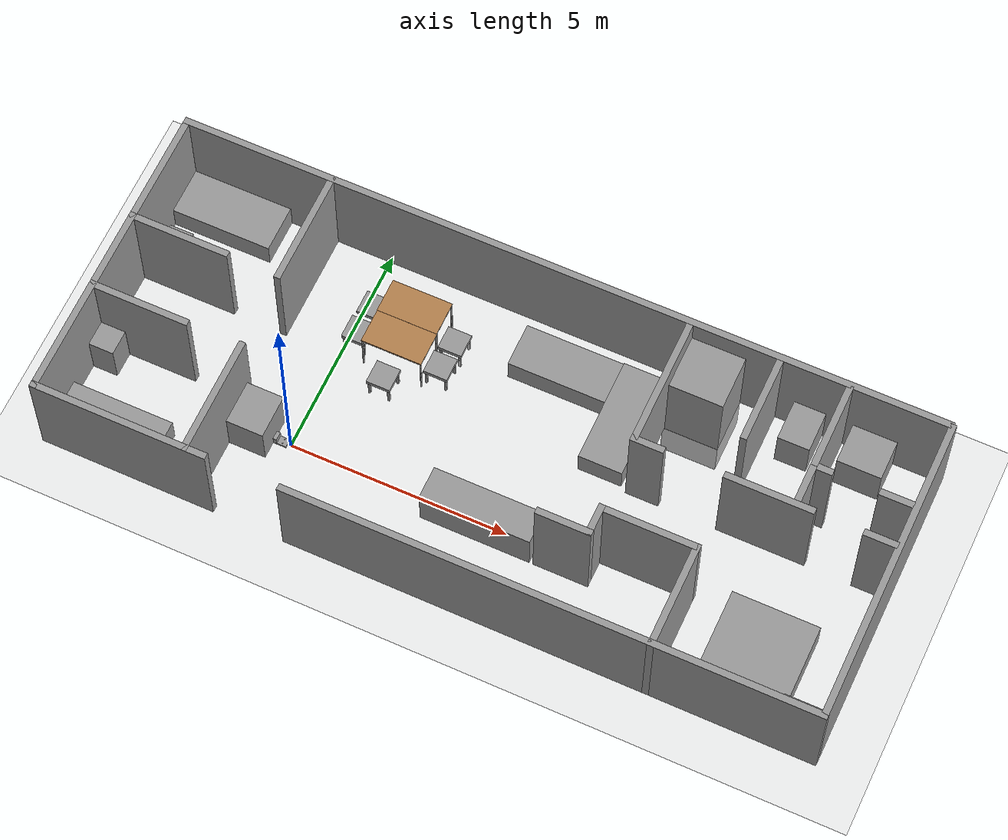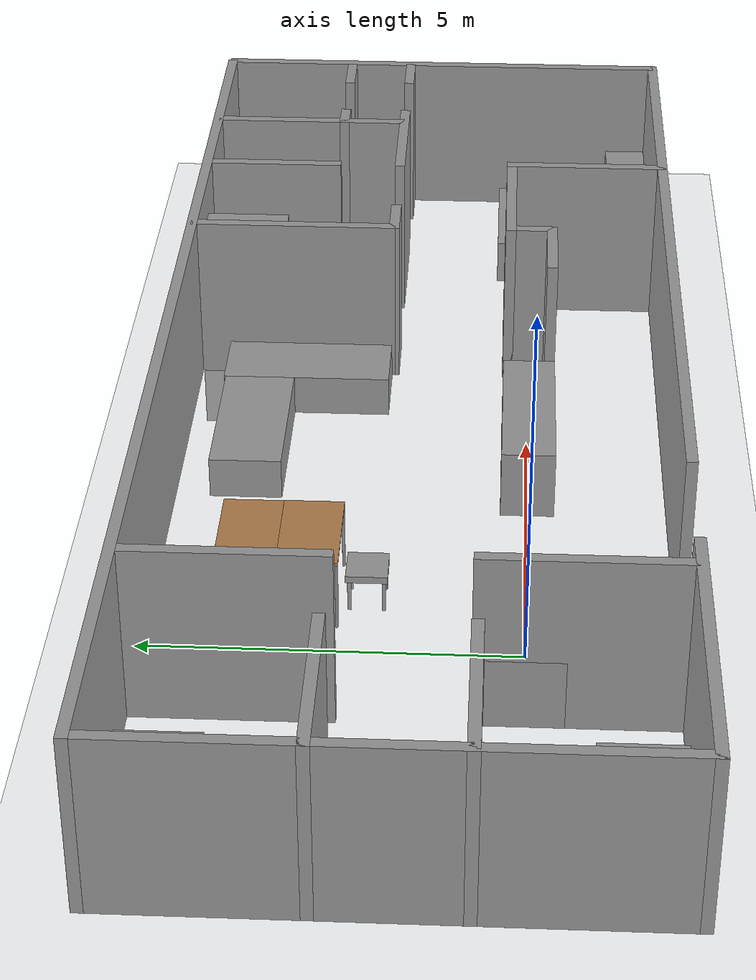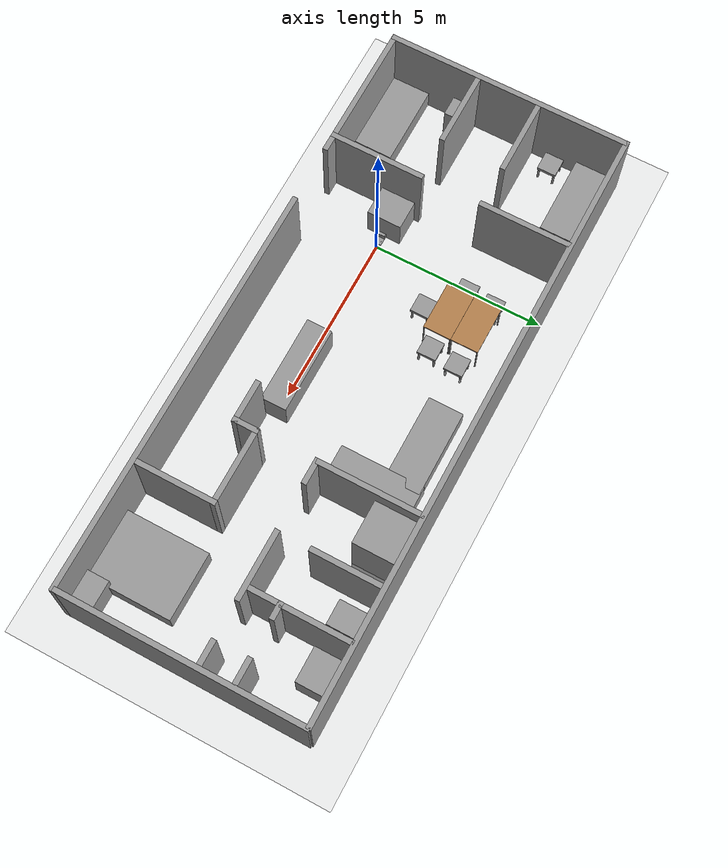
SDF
<sdf version="1.6">
 <world name="default">
  <light name="sun" type="directional">
   <pose>0 0 10 0 -0 0</pose>
   <diffuse>0.8 0.8 0.8 1</diffuse>
   <specular>0.1 0.1 0.1 1</specular>
   <attenuation>
    <range>1000</range>
    <constant>0.9</constant>
    <linear>0.01</linear>
    <quadratic>0.001</quadratic>
   </attenuation>
   <direction>-0.5 0.5 -1</direction>
  </light>
  <model name="ground_plane">
   <static>1</static>
   <link name="link">
    <collision name="collision">
     <geometry><plane><normal>0 0 1</normal><size>100 100</size></plane></geometry>
     <surface><friction><ode><mu>100</mu><mu2>50</mu2></ode></friction></surface>
    </collision>
    <visual name="visual">
     <cast_shadows>0</cast_shadows>
     <geometry><plane><normal>0 0 1</normal><size>100 100</size></plane></geometry>
     <material>
      <script><uri>file://media/materials/scripts/gazebo.material</uri><name>Gazebo/Grey</name></script>
     </material>
    </visual>
   </link>
  </model>
  <gravity>0 0 -9.8</gravity>
  <magnetic_field>6e-06 2.3e-05 -4.2e-05</magnetic_field>
  <atmosphere type="adiabatic"/>
  <physics name="default_physics" default="0" type="ode">
   <max_step_size>0.001</max_step_size>
   <real_time_factor>1</real_time_factor>
   <real_time_update_rate>1000</real_time_update_rate>
  </physics>
  <scene><ambient>0.4 0.4 0.4 1</ambient><background>0.7 0.7 0.7 1</background><shadows>1</shadows></scene>
  <spherical_coordinates>
   <surface_model>EARTH_WGS84</surface_model>
   <latitude_deg>0</latitude_deg>
   <longitude_deg>0</longitude_deg>
   <elevation>0</elevation>
   <heading_deg>0</heading_deg>
  </spherical_coordinates>
  <model name="gobot_world">
   <link name="Wall_28">
    <pose>-7.13865 -3.175 0 0 -0 3.14159</pose>
    <inertial>
     <inertia><ixx>nan</ixx><ixy>0</ixy><ixz>0</ixz><iyy>nan</iyy><iyz>0</iyz><izz>nan</izz></inertia>
     <mass>0</mass>
    </inertial>
    <visual name="Wall_28_Visual">
     <pose>0 0 1.25 0 -0 0</pose>
     <geometry><box><size>4.03984 0.15 2.5</size></box></geometry>
     <material>
      <script><uri>file://media/materials/scripts/gazebo.material</uri><name>Gazebo/Grey</name></script>
      <ambient>1 1 1 1</ambient>
      <diffuse>0.7 0.7 0.7 1</diffuse>
      <specular>0.01 0.01 0.01 1</specular>
      <emissive>0 0 0 1</emissive>
     </material>
    </visual>
    <collision name="Wall_28_Collision">
     <pose>0 0 1.25 0 -0 0</pose>
     <geometry><box><size>4.03984 0.15 2.5</size></box></geometry>
     <surface>
      <friction>
       <ode><mu>1</mu><mu2>1</mu2><fdir1>0 0 0</fdir1><slip1>0</slip1><slip2>0</slip2></ode>
       <torsional>
        <coefficient>1</coefficient>
        <patch_radius>0</patch_radius>
        <surface_radius>0</surface_radius>
        <use_patch_radius>1</use_patch_radius>
        <ode><slip>0</slip></ode>
       </torsional>
      </friction>
      <bounce><restitution_coefficient>0</restitution_coefficient><threshold>1e+06</threshold></bounce>
      <contact>
       <collide_without_contact>0</collide_without_contact>
       <collide_without_contact_bitmask>1</collide_without_contact_bitmask>
       <collide_bitmask>1</collide_bitmask>
       <ode>
        <soft_cfm>0</soft_cfm>
        <soft_erp>0.2</soft_erp>
        <kp>1e+13</kp>
        <kd>1</kd>
        <max_vel>0.01</max_vel>
        <min_depth>0</min_depth>
       </ode>
       <bullet>
        <split_impulse>1</split_impulse>
        <split_impulse_penetration_threshold>-0.01</split_impulse_penetration_threshold>
        <soft_cfm>0</soft_cfm>
        <soft_erp>0.2</soft_erp>
        <kp>1e+13</kp>
        <kd>1</kd>
       </bullet>
      </contact>
     </surface>
    </collision>
   </link>
   <link name="Wall_29">
    <pose>-9.08356 0.297477 0 0 -0 1.5708</pose>
    <inertial>
     <inertia><ixx>nan</ixx><ixy>0</ixy><ixz>0</ixz><iyy>nan</iyy><iyz>0</iyz><izz>nan</izz></inertia>
     <mass>0</mass>
    </inertial>
    <visual name="Wall_29_Visual">
     <pose>0 0 1.25 0 -0 0</pose>
     <geometry><box><size>7.07952 0.15 2.5</size></box></geometry>
     <material>
      <script><uri>file://media/materials/scripts/gazebo.material</uri><name>Gazebo/Grey</name></script>
      <ambient>1 1 1 1</ambient>
      <diffuse>0.7 0.7 0.7 1</diffuse>
      <specular>0.01 0.01 0.01 1</specular>
      <emissive>0 0 0 1</emissive>
     </material>
    </visual>
    <collision name="Wall_29_Collision">
     <pose>0 0 1.25 0 -0 0</pose>
     <geometry><box><size>7.07952 0.15 2.5</size></box></geometry>
     <surface>
      <friction>
       <ode><mu>1</mu><mu2>1</mu2><fdir1>0 0 0</fdir1><slip1>0</slip1><slip2>0</slip2></ode>
       <torsional>
        <coefficient>1</coefficient>
        <patch_radius>0</patch_radius>
        <surface_radius>0</surface_radius>
        <use_patch_radius>1</use_patch_radius>
        <ode><slip>0</slip></ode>
       </torsional>
      </friction>
      <bounce><restitution_coefficient>0</restitution_coefficient><threshold>1e+06</threshold></bounce>
      <contact>
       <collide_without_contact>0</collide_without_contact>
       <collide_without_contact_bitmask>1</collide_without_contact_bitmask>
       <collide_bitmask>1</collide_bitmask>
       <ode>
        <soft_cfm>0</soft_cfm>
        <soft_erp>0.2</soft_erp>
        <kp>1e+13</kp>
        <kd>1</kd>
        <max_vel>0.01</max_vel>
        <min_depth>0</min_depth>
       </ode>
       <bullet>
        <split_impulse>1</split_impulse>
        <split_impulse_penetration_threshold>-0.01</split_impulse_penetration_threshold>
        <soft_cfm>0</soft_cfm>
        <soft_erp>0.2</soft_erp>
        <kp>1e+13</kp>
        <kd>1</kd>
       </bullet>
      </contact>
     </surface>
    </collision>
   </link>
   <link name="Wall_30">
    <pose>-0.35753 3.79808 0 0 -0 0</pose>
    <inertial>
     <inertia><ixx>nan</ixx><ixy>0</ixy><ixz>0</ixz><iyy>nan</iyy><iyz>0</iyz><izz>nan</izz></inertia>
     <mass>0</mass>
    </inertial>
    <visual name="Wall_30_Visual">
     <pose>0 0 1.25 0 -0 0</pose>
     <geometry><box><size>17.6021 0.15 2.5</size></box></geometry>
     <material>
      <script><uri>file://media/materials/scripts/gazebo.material</uri><name>Gazebo/Grey</name></script>
      <ambient>1 1 1 1</ambient>
      <diffuse>0.7 0.7 0.7 1</diffuse>
      <specular>0.01 0.01 0.01 1</specular>
      <emissive>0 0 0 1</emissive>
     </material>
    </visual>
    <collision name="Wall_30_Collision">
     <pose>0 0 1.25 0 -0 0</pose>
     <geometry><box><size>17.6021 0.15 2.5</size></box></geometry>
     <surface>
      <friction>
       <ode><mu>1</mu><mu2>1</mu2><fdir1>0 0 0</fdir1><slip1>0</slip1><slip2>0</slip2></ode>
       <torsional>
        <coefficient>1</coefficient>
        <patch_radius>0</patch_radius>
        <surface_radius>0</surface_radius>
        <use_patch_radius>1</use_patch_radius>
        <ode><slip>0</slip></ode>
       </torsional>
      </friction>
      <bounce><restitution_coefficient>0</restitution_coefficient><threshold>1e+06</threshold></bounce>
      <contact>
       <collide_without_contact>0</collide_without_contact>
       <collide_without_contact_bitmask>1</collide_without_contact_bitmask>
       <collide_bitmask>1</collide_bitmask>
       <ode>
        <soft_cfm>0</soft_cfm>
        <soft_erp>0.2</soft_erp>
        <kp>1e+13</kp>
        <kd>1</kd>
        <max_vel>0.01</max_vel>
        <min_depth>0</min_depth>
       </ode>
       <bullet>
        <split_impulse>1</split_impulse>
        <split_impulse_penetration_threshold>-0.01</split_impulse_penetration_threshold>
        <soft_cfm>0</soft_cfm>
        <soft_erp>0.2</soft_erp>
        <kp>1e+13</kp>
        <kd>1</kd>
       </bullet>
      </contact>
     </surface>
    </collision>
   </link>
   <link name="Wall_31">
    <pose>8.425 0.325252 0 0 0 -1.5708</pose>
    <inertial>
     <inertia><ixx>nan</ixx><ixy>0</ixy><ixz>0</ixz><iyy>nan</iyy><iyz>0</iyz><izz>nan</izz></inertia>
     <mass>0</mass>
    </inertial>
    <visual name="Wall_31_Visual">
     <pose>0 0 1.25 0 -0 0</pose>
     <geometry><box><size>7.00949 0.15 2.5</size></box></geometry>
     <material>
      <script><uri>file://media/materials/scripts/gazebo.material</uri><name>Gazebo/Grey</name></script>
      <ambient>1 1 1 1</ambient>
      <diffuse>0.7 0.7 0.7 1</diffuse>
      <specular>0.01 0.01 0.01 1</specular>
      <emissive>0 0 0 1</emissive>
     </material>
    </visual>
    <collision name="Wall_31_Collision">
     <pose>0 0 1.25 0 -0 0</pose>
     <geometry><box><size>7.00949 0.15 2.5</size></box></geometry>
     <surface>
      <friction>
       <ode><mu>1</mu><mu2>1</mu2><fdir1>0 0 0</fdir1><slip1>0</slip1><slip2>0</slip2></ode>
       <torsional>
        <coefficient>1</coefficient>
        <patch_radius>0</patch_radius>
        <surface_radius>0</surface_radius>
        <use_patch_radius>1</use_patch_radius>
        <ode><slip>0</slip></ode>
       </torsional>
      </friction>
      <bounce><restitution_coefficient>0</restitution_coefficient><threshold>1e+06</threshold></bounce>
      <contact>
       <collide_without_contact>0</collide_without_contact>
       <collide_without_contact_bitmask>1</collide_without_contact_bitmask>
       <collide_bitmask>1</collide_bitmask>
       <ode>
        <soft_cfm>0</soft_cfm>
        <soft_erp>0.2</soft_erp>
        <kp>1e+13</kp>
        <kd>1</kd>
        <max_vel>0.01</max_vel>
        <min_depth>0</min_depth>
       </ode>
       <bullet>
        <split_impulse>1</split_impulse>
        <split_impulse_penetration_threshold>-0.01</split_impulse_penetration_threshold>
        <soft_cfm>0</soft_cfm>
        <soft_erp>0.2</soft_erp>
        <kp>1e+13</kp>
        <kd>1</kd>
       </bullet>
      </contact>
     </surface>
    </collision>
   </link>
   <link name="Wall_32">
    <pose>2.5 -3.175 0 0 -0 3.14159</pose>
    <visual name="Wall_32_Visual">
     <pose>0 0 1.25 0 -0 0</pose>
     <geometry><box><size>12 0.15 2.5</size></box></geometry>
     <material>
      <script><uri>file://media/materials/scripts/gazebo.material</uri><name>Gazebo/Grey</name></script>
      <ambient>1 1 1 1</ambient>
      <diffuse>0.7 0.7 0.7 1</diffuse>
      <specular>0.01 0.01 0.01 1</specular>
      <emissive>0 0 0 1</emissive>
     </material>
    </visual>
    <collision name="Wall_32_Collision">
     <pose>0 0 1.25 0 -0 0</pose>
     <geometry><box><size>12 0.15 2.5</size></box></geometry>
     <surface>
      <friction>
       <ode><mu>1</mu><mu2>1</mu2><fdir1>0 0 0</fdir1><slip1>0</slip1><slip2>0</slip2></ode>
       <torsional>
        <coefficient>1</coefficient>
        <patch_radius>0</patch_radius>
        <surface_radius>0</surface_radius>
        <use_patch_radius>1</use_patch_radius>
        <ode><slip>0</slip></ode>
       </torsional>
      </friction>
      <bounce><restitution_coefficient>0</restitution_coefficient><threshold>1e+06</threshold></bounce>
      <contact>
       <collide_without_contact>0</collide_without_contact>
       <collide_without_contact_bitmask>1</collide_without_contact_bitmask>
       <collide_bitmask>1</collide_bitmask>
       <ode>
        <soft_cfm>0</soft_cfm>
        <soft_erp>0.2</soft_erp>
        <kp>1e+13</kp>
        <kd>1</kd>
        <max_vel>0.01</max_vel>
        <min_depth>0</min_depth>
       </ode>
       <bullet>
        <split_impulse>1</split_impulse>
        <split_impulse_penetration_threshold>-0.01</split_impulse_penetration_threshold>
        <soft_cfm>0</soft_cfm>
        <soft_erp>0.2</soft_erp>
        <kp>1e+13</kp>
        <kd>1</kd>
       </bullet>
      </contact>
     </surface>
    </collision>
   </link>
   <link name="Wall_38">
    <pose>-5.62251 -1.875 0 0 -0 1.5708</pose>
    <visual name="Wall_38_Visual">
     <pose>0 0 1.25 0 -0 0</pose>
     <geometry><box><size>2.75 0.15 2.5</size></box></geometry>
     <material>
      <script><uri>file://media/materials/scripts/gazebo.material</uri><name>Gazebo/Grey</name></script>
      <ambient>1 1 1 1</ambient>
      <diffuse>0.7 0.7 0.7 1</diffuse>
      <specular>0.01 0.01 0.01 1</specular>
      <emissive>0 0 0 1</emissive>
     </material>
    </visual>
    <collision name="Wall_38_Collision">
     <pose>0 0 1.25 0 -0 0</pose>
     <geometry><box><size>2.75 0.15 2.5</size></box></geometry>
     <surface>
      <friction>
       <ode><mu>1</mu><mu2>1</mu2><fdir1>0 0 0</fdir1><slip1>0</slip1><slip2>0</slip2></ode>
       <torsional>
        <coefficient>1</coefficient>
        <patch_radius>0</patch_radius>
        <surface_radius>0</surface_radius>
        <use_patch_radius>1</use_patch_radius>
        <ode><slip>0</slip></ode>
       </torsional>
      </friction>
      <bounce><restitution_coefficient>0</restitution_coefficient><threshold>1e+06</threshold></bounce>
      <contact>
       <collide_without_contact>0</collide_without_contact>
       <collide_without_contact_bitmask>1</collide_without_contact_bitmask>
       <collide_bitmask>1</collide_bitmask>
       <ode>
        <soft_cfm>0</soft_cfm>
        <soft_erp>0.2</soft_erp>
        <kp>1e+13</kp>
        <kd>1</kd>
        <max_vel>0.01</max_vel>
        <min_depth>0</min_depth>
       </ode>
       <bullet>
        <split_impulse>1</split_impulse>
        <split_impulse_penetration_threshold>-0.01</split_impulse_penetration_threshold>
        <soft_cfm>0</soft_cfm>
        <soft_erp>0.2</soft_erp>
        <kp>1e+13</kp>
        <kd>1</kd>
       </bullet>
      </contact>
     </surface>
    </collision>
   </link>
   <link name="Wall_40">
    <pose>-5.65293 2.49165 0 0 0 -1.5708</pose>
    <inertial>
     <inertia><ixx>nan</ixx><ixy>0</ixy><ixz>0</ixz><iyy>nan</iyy><iyz>0</iyz><izz>nan</izz></inertia>
     <mass>0</mass>
    </inertial>
    <visual name="Wall_40_Visual">
     <pose>0 0 1.25 0 -0 0</pose>
     <geometry><box><size>2.68286 0.15 2.5</size></box></geometry>
     <material>
      <script><uri>file://media/materials/scripts/gazebo.material</uri><name>Gazebo/Grey</name></script>
      <ambient>1 1 1 1</ambient>
      <diffuse>0.7 0.7 0.7 1</diffuse>
      <specular>0.01 0.01 0.01 1</specular>
      <emissive>0 0 0 1</emissive>
     </material>
    </visual>
    <collision name="Wall_40_Collision">
     <pose>0 0 1.25 0 -0 0</pose>
     <geometry><box><size>2.68286 0.15 2.5</size></box></geometry>
     <surface>
      <friction>
       <ode><mu>1</mu><mu2>1</mu2><fdir1>0 0 0</fdir1><slip1>0</slip1><slip2>0</slip2></ode>
       <torsional>
        <coefficient>1</coefficient>
        <patch_radius>0</patch_radius>
        <surface_radius>0</surface_radius>
        <use_patch_radius>1</use_patch_radius>
        <ode><slip>0</slip></ode>
       </torsional>
      </friction>
      <bounce><restitution_coefficient>0</restitution_coefficient><threshold>1e+06</threshold></bounce>
      <contact>
       <collide_without_contact>0</collide_without_contact>
       <collide_without_contact_bitmask>1</collide_without_contact_bitmask>
       <collide_bitmask>1</collide_bitmask>
       <ode>
        <soft_cfm>0</soft_cfm>
        <soft_erp>0.2</soft_erp>
        <kp>1e+13</kp>
        <kd>1</kd>
        <max_vel>0.01</max_vel>
        <min_depth>0</min_depth>
       </ode>
       <bullet>
        <split_impulse>1</split_impulse>
        <split_impulse_penetration_threshold>-0.01</split_impulse_penetration_threshold>
        <soft_cfm>0</soft_cfm>
        <soft_erp>0.2</soft_erp>
        <kp>1e+13</kp>
        <kd>1</kd>
       </bullet>
      </contact>
     </surface>
    </collision>
   </link>
   <link name="Wall_42">
    <pose>-7.9911 1.23404 0 0 -0 0</pose>
    <inertial>
     <inertia><ixx>nan</ixx><ixy>0</ixy><ixz>0</ixz><iyy>nan</iyy><iyz>0</iyz><izz>nan</izz></inertia>
     <mass>0</mass>
    </inertial>
    <visual name="Wall_42_Visual">
     <pose>0 0 1.25 0 -0 0</pose>
     <geometry><box><size>2.33494 0.15 2.5</size></box></geometry>
     <material>
      <script><uri>file://media/materials/scripts/gazebo.material</uri><name>Gazebo/Grey</name></script>
      <ambient>1 1 1 1</ambient>
      <diffuse>0.7 0.7 0.7 1</diffuse>
      <specular>0.01 0.01 0.01 1</specular>
      <emissive>0 0 0 1</emissive>
     </material>
    </visual>
    <collision name="Wall_42_Collision">
     <pose>0 0 1.25 0 -0 0</pose>
     <geometry><box><size>2.33494 0.15 2.5</size></box></geometry>
     <surface>
      <friction>
       <ode><mu>1</mu><mu2>1</mu2><fdir1>0 0 0</fdir1><slip1>0</slip1><slip2>0</slip2></ode>
       <torsional>
        <coefficient>1</coefficient>
        <patch_radius>0</patch_radius>
        <surface_radius>0</surface_radius>
        <use_patch_radius>1</use_patch_radius>
        <ode><slip>0</slip></ode>
       </torsional>
      </friction>
      <bounce><restitution_coefficient>0</restitution_coefficient><threshold>1e+06</threshold></bounce>
      <contact>
       <collide_without_contact>0</collide_without_contact>
       <collide_without_contact_bitmask>1</collide_without_contact_bitmask>
       <collide_bitmask>1</collide_bitmask>
       <ode>
        <soft_cfm>0</soft_cfm>
        <soft_erp>0.2</soft_erp>
        <kp>1e+13</kp>
        <kd>1</kd>
        <max_vel>0.01</max_vel>
        <min_depth>0</min_depth>
       </ode>
       <bullet>
        <split_impulse>1</split_impulse>
        <split_impulse_penetration_threshold>-0.01</split_impulse_penetration_threshold>
        <soft_cfm>0</soft_cfm>
        <soft_erp>0.2</soft_erp>
        <kp>1e+13</kp>
        <kd>1</kd>
       </bullet>
      </contact>
     </surface>
    </collision>
   </link>
   <link name="Wall_44">
    <pose>-8.00404 -0.574303 0 0 -0 0</pose>
    <inertial>
     <inertia><ixx>nan</ixx><ixy>0</ixy><ixz>0</ixz><iyy>nan</iyy><iyz>0</iyz><izz>nan</izz></inertia>
     <mass>0</mass>
    </inertial>
    <visual name="Wall_44_Visual">
     <pose>0 0 1.25 0 -0 0</pose>
     <geometry><box><size>2.30905 0.15 2.5</size></box></geometry>
     <material>
      <script><uri>file://media/materials/scripts/gazebo.material</uri><name>Gazebo/Grey</name></script>
      <ambient>1 1 1 1</ambient>
      <diffuse>0.7 0.7 0.7 1</diffuse>
      <specular>0.01 0.01 0.01 1</specular>
      <emissive>0 0 0 1</emissive>
     </material>
    </visual>
    <collision name="Wall_44_Collision">
     <pose>0 0 1.25 0 -0 0</pose>
     <geometry><box><size>2.30905 0.15 2.5</size></box></geometry>
     <surface>
      <friction>
       <ode><mu>1</mu><mu2>1</mu2><fdir1>0 0 0</fdir1><slip1>0</slip1><slip2>0</slip2></ode>
       <torsional>
        <coefficient>1</coefficient>
        <patch_radius>0</patch_radius>
        <surface_radius>0</surface_radius>
        <use_patch_radius>1</use_patch_radius>
        <ode><slip>0</slip></ode>
       </torsional>
      </friction>
      <bounce><restitution_coefficient>0</restitution_coefficient><threshold>1e+06</threshold></bounce>
      <contact>
       <collide_without_contact>0</collide_without_contact>
       <collide_without_contact_bitmask>1</collide_without_contact_bitmask>
       <collide_bitmask>1</collide_bitmask>
       <ode>
        <soft_cfm>0</soft_cfm>
        <soft_erp>0.2</soft_erp>
        <kp>1e+13</kp>
        <kd>1</kd>
        <max_vel>0.01</max_vel>
        <min_depth>0</min_depth>
       </ode>
       <bullet>
        <split_impulse>1</split_impulse>
        <split_impulse_penetration_threshold>-0.01</split_impulse_penetration_threshold>
        <soft_cfm>0</soft_cfm>
        <soft_erp>0.2</soft_erp>
        <kp>1e+13</kp>
        <kd>1</kd>
       </bullet>
      </contact>
     </surface>
    </collision>
   </link>
   <link name="Wall_46">
    <pose>4.73464 -2.02799 0 0 -0 1.5708</pose>
    <inertial>
     <inertia><ixx>nan</ixx><ixy>0</ixy><ixz>0</ixz><iyy>nan</iyy><iyz>0</iyz><izz>nan</izz></inertia>
     <mass>0</mass>
    </inertial>
    <visual name="Wall_46_Visual">
     <pose>0 0 1.25 0 -0 0</pose>
     <geometry><box><size>2.44404 0.15 2.5</size></box></geometry>
     <material>
      <script><uri>file://media/materials/scripts/gazebo.material</uri><name>Gazebo/Grey</name></script>
      <ambient>1 1 1 1</ambient>
      <diffuse>0.7 0.7 0.7 1</diffuse>
      <specular>0.01 0.01 0.01 1</specular>
      <emissive>0 0 0 1</emissive>
     </material>
    </visual>
    <collision name="Wall_46_Collision">
     <pose>0 0 1.25 0 -0 0</pose>
     <geometry><box><size>2.44404 0.15 2.5</size></box></geometry>
     <surface>
      <friction>
       <ode><mu>1</mu><mu2>1</mu2><fdir1>0 0 0</fdir1><slip1>0</slip1><slip2>0</slip2></ode>
       <torsional>
        <coefficient>1</coefficient>
        <patch_radius>0</patch_radius>
        <surface_radius>0</surface_radius>
        <use_patch_radius>1</use_patch_radius>
        <ode><slip>0</slip></ode>
       </torsional>
      </friction>
      <bounce><restitution_coefficient>0</restitution_coefficient><threshold>1e+06</threshold></bounce>
      <contact>
       <collide_without_contact>0</collide_without_contact>
       <collide_without_contact_bitmask>1</collide_without_contact_bitmask>
       <collide_bitmask>1</collide_bitmask>
       <ode>
        <soft_cfm>0</soft_cfm>
        <soft_erp>0.2</soft_erp>
        <kp>1e+13</kp>
        <kd>1</kd>
        <max_vel>0.01</max_vel>
        <min_depth>0</min_depth>
       </ode>
       <bullet>
        <split_impulse>1</split_impulse>
        <split_impulse_penetration_threshold>-0.01</split_impulse_penetration_threshold>
        <soft_cfm>0</soft_cfm>
        <soft_erp>0.2</soft_erp>
        <kp>1e+13</kp>
        <kd>1</kd>
       </bullet>
      </contact>
     </surface>
    </collision>
   </link>
   <link name="Wall_48">
    <pose>5.59881 0.836641 0 0 -0 0</pose>
    <visual name="Wall_48_Visual">
     <pose>0 0 1.25 0 -0 0</pose>
     <geometry><box><size>2 0.15 2.5</size></box></geometry>
     <material>
      <script><uri>file://media/materials/scripts/gazebo.material</uri><name>Gazebo/Grey</name></script>
      <ambient>1 1 1 1</ambient>
      <diffuse>0.7 0.7 0.7 1</diffuse>
      <specular>0.01 0.01 0.01 1</specular>
      <emissive>0 0 0 1</emissive>
     </material>
    </visual>
    <collision name="Wall_48_Collision">
     <pose>0 0 1.25 0 -0 0</pose>
     <geometry><box><size>2 0.15 2.5</size></box></geometry>
     <surface>
      <friction>
       <ode><mu>1</mu><mu2>1</mu2><fdir1>0 0 0</fdir1><slip1>0</slip1><slip2>0</slip2></ode>
       <torsional>
        <coefficient>1</coefficient>
        <patch_radius>0</patch_radius>
        <surface_radius>0</surface_radius>
        <use_patch_radius>1</use_patch_radius>
        <ode><slip>0</slip></ode>
       </torsional>
      </friction>
      <bounce><restitution_coefficient>0</restitution_coefficient><threshold>1e+06</threshold></bounce>
      <contact>
       <collide_without_contact>0</collide_without_contact>
       <collide_without_contact_bitmask>1</collide_without_contact_bitmask>
       <collide_bitmask>1</collide_bitmask>
       <ode>
        <soft_cfm>0</soft_cfm>
        <soft_erp>0.2</soft_erp>
        <kp>1e+13</kp>
        <kd>1</kd>
        <max_vel>0.01</max_vel>
        <min_depth>0</min_depth>
       </ode>
       <bullet>
        <split_impulse>1</split_impulse>
        <split_impulse_penetration_threshold>-0.01</split_impulse_penetration_threshold>
        <soft_cfm>0</soft_cfm>
        <soft_erp>0.2</soft_erp>
        <kp>1e+13</kp>
        <kd>1</kd>
       </bullet>
      </contact>
     </surface>
    </collision>
   </link>
   <link name="Wall_50">
    <pose>8.02222 0.823342 0 0 -0 0</pose>
    <visual name="Wall_50_Visual">
     <pose>0 0 1.25 0 -0 0</pose>
     <geometry><box><size>0.75 0.15 2.5</size></box></geometry>
     <material>
      <script><uri>file://media/materials/scripts/gazebo.material</uri><name>Gazebo/Grey</name></script>
      <ambient>1 1 1 1</ambient>
      <diffuse>0.7 0.7 0.7 1</diffuse>
      <specular>0.01 0.01 0.01 1</specular>
      <emissive>0 0 0 1</emissive>
     </material>
    </visual>
    <collision name="Wall_50_Collision">
     <pose>0 0 1.25 0 -0 0</pose>
     <geometry><box><size>0.75 0.15 2.5</size></box></geometry>
     <surface>
      <friction>
       <ode><mu>1</mu><mu2>1</mu2><fdir1>0 0 0</fdir1><slip1>0</slip1><slip2>0</slip2></ode>
       <torsional>
        <coefficient>1</coefficient>
        <patch_radius>0</patch_radius>
        <surface_radius>0</surface_radius>
        <use_patch_radius>1</use_patch_radius>
        <ode><slip>0</slip></ode>
       </torsional>
      </friction>
      <bounce><restitution_coefficient>0</restitution_coefficient><threshold>1e+06</threshold></bounce>
      <contact>
       <collide_without_contact>0</collide_without_contact>
       <collide_without_contact_bitmask>1</collide_without_contact_bitmask>
       <collide_bitmask>1</collide_bitmask>
       <ode>
        <soft_cfm>0</soft_cfm>
        <soft_erp>0.2</soft_erp>
        <kp>1e+13</kp>
        <kd>1</kd>
        <max_vel>0.01</max_vel>
        <min_depth>0</min_depth>
       </ode>
       <bullet>
        <split_impulse>1</split_impulse>
        <split_impulse_penetration_threshold>-0.01</split_impulse_penetration_threshold>
        <soft_cfm>0</soft_cfm>
        <soft_erp>0.2</soft_erp>
        <kp>1e+13</kp>
        <kd>1</kd>
       </bullet>
      </contact>
     </surface>
    </collision>
   </link>
   <link name="Wall_52">
    <pose>6.17948 1.33418 0 0 -0 1.5708</pose>
    <visual name="Wall_52_Visual">
     <pose>0 0 1.25 0 -0 0</pose>
     <geometry><box><size>1 0.15 2.5</size></box></geometry>
     <material>
      <script><uri>file://media/materials/scripts/gazebo.material</uri><name>Gazebo/Grey</name></script>
      <ambient>1 1 1 1</ambient>
      <diffuse>0.7 0.7 0.7 1</diffuse>
      <specular>0.01 0.01 0.01 1</specular>
      <emissive>0 0 0 1</emissive>
     </material>
    </visual>
    <collision name="Wall_52_Collision">
     <pose>0 0 1.25 0 -0 0</pose>
     <geometry><box><size>1 0.15 2.5</size></box></geometry>
     <surface>
      <friction>
       <ode><mu>1</mu><mu2>1</mu2><fdir1>0 0 0</fdir1><slip1>0</slip1><slip2>0</slip2></ode>
       <torsional>
        <coefficient>1</coefficient>
        <patch_radius>0</patch_radius>
        <surface_radius>0</surface_radius>
        <use_patch_radius>1</use_patch_radius>
        <ode><slip>0</slip></ode>
       </torsional>
      </friction>
      <bounce><restitution_coefficient>0</restitution_coefficient><threshold>1e+06</threshold></bounce>
      <contact>
       <collide_without_contact>0</collide_without_contact>
       <collide_without_contact_bitmask>1</collide_without_contact_bitmask>
       <collide_bitmask>1</collide_bitmask>
       <ode>
        <soft_cfm>0</soft_cfm>
        <soft_erp>0.2</soft_erp>
        <kp>1e+13</kp>
        <kd>1</kd>
        <max_vel>0.01</max_vel>
        <min_depth>0</min_depth>
       </ode>
       <bullet>
        <split_impulse>1</split_impulse>
        <split_impulse_penetration_threshold>-0.01</split_impulse_penetration_threshold>
        <soft_cfm>0</soft_cfm>
        <soft_erp>0.2</soft_erp>
        <kp>1e+13</kp>
        <kd>1</kd>
       </bullet>
      </contact>
     </surface>
    </collision>
   </link>
   <link name="Wall_55">
    <pose>6.35447 1.78862 0 0 -0 0</pose>
    <visual name="Wall_55_Visual">
     <pose>0 0 1.25 0 -0 0</pose>
     <geometry><box><size>0.5 0.15 2.5</size></box></geometry>
     <material>
      <script><uri>file://media/materials/scripts/gazebo.material</uri><name>Gazebo/Grey</name></script>
      <ambient>1 1 1 1</ambient>
      <diffuse>0.7 0.7 0.7 1</diffuse>
      <specular>0.01 0.01 0.01 1</specular>
      <emissive>0 0 0 1</emissive>
     </material>
    </visual>
    <collision name="Wall_55_Collision">
     <pose>0 0 1.25 0 -0 0</pose>
     <geometry><box><size>0.5 0.15 2.5</size></box></geometry>
     <surface>
      <friction>
       <ode><mu>1</mu><mu2>1</mu2><fdir1>0 0 0</fdir1><slip1>0</slip1><slip2>0</slip2></ode>
       <torsional>
        <coefficient>1</coefficient>
        <patch_radius>0</patch_radius>
        <surface_radius>0</surface_radius>
        <use_patch_radius>1</use_patch_radius>
        <ode><slip>0</slip></ode>
       </torsional>
      </friction>
      <bounce><restitution_coefficient>0</restitution_coefficient><threshold>1e+06</threshold></bounce>
      <contact>
       <collide_without_contact>0</collide_without_contact>
       <collide_without_contact_bitmask>1</collide_without_contact_bitmask>
       <collide_bitmask>1</collide_bitmask>
       <ode>
        <soft_cfm>0</soft_cfm>
        <soft_erp>0.2</soft_erp>
        <kp>1e+13</kp>
        <kd>1</kd>
        <max_vel>0.01</max_vel>
        <min_depth>0</min_depth>
       </ode>
       <bullet>
        <split_impulse>1</split_impulse>
        <split_impulse_penetration_threshold>-0.01</split_impulse_penetration_threshold>
        <soft_cfm>0</soft_cfm>
        <soft_erp>0.2</soft_erp>
        <kp>1e+13</kp>
        <kd>1</kd>
       </bullet>
      </contact>
     </surface>
    </collision>
   </link>
   <link name="Wall_57">
    <pose>7.98514 1.792 0 0 -0 0</pose>
    <visual name="Wall_57_Visual">
     <pose>0 0 1.25 0 -0 0</pose>
     <geometry><box><size>0.75 0.15 2.5</size></box></geometry>
     <material>
      <script><uri>file://media/materials/scripts/gazebo.material</uri><name>Gazebo/Grey</name></script>
      <ambient>1 1 1 1</ambient>
      <diffuse>0.7 0.7 0.7 1</diffuse>
      <specular>0.01 0.01 0.01 1</specular>
      <emissive>0 0 0 1</emissive>
     </material>
    </visual>
    <collision name="Wall_57_Collision">
     <pose>0 0 1.25 0 -0 0</pose>
     <geometry><box><size>0.75 0.15 2.5</size></box></geometry>
     <surface>
      <friction>
       <ode><mu>1</mu><mu2>1</mu2><fdir1>0 0 0</fdir1><slip1>0</slip1><slip2>0</slip2></ode>
       <torsional>
        <coefficient>1</coefficient>
        <patch_radius>0</patch_radius>
        <surface_radius>0</surface_radius>
        <use_patch_radius>1</use_patch_radius>
        <ode><slip>0</slip></ode>
       </torsional>
      </friction>
      <bounce><restitution_coefficient>0</restitution_coefficient><threshold>1e+06</threshold></bounce>
      <contact>
       <collide_without_contact>0</collide_without_contact>
       <collide_without_contact_bitmask>1</collide_without_contact_bitmask>
       <collide_bitmask>1</collide_bitmask>
       <ode>
        <soft_cfm>0</soft_cfm>
        <soft_erp>0.2</soft_erp>
        <kp>1e+13</kp>
        <kd>1</kd>
        <max_vel>0.01</max_vel>
        <min_depth>0</min_depth>
       </ode>
       <bullet>
        <split_impulse>1</split_impulse>
        <split_impulse_penetration_threshold>-0.01</split_impulse_penetration_threshold>
        <soft_cfm>0</soft_cfm>
        <soft_erp>0.2</soft_erp>
        <kp>1e+13</kp>
        <kd>1</kd>
       </bullet>
      </contact>
     </surface>
    </collision>
   </link>
   <link name="Wall_59">
    <pose>6.17948 2.77727 0 0 -0 1.5708</pose>
    <visual name="Wall_59_Visual">
     <pose>0 0 1.25 0 -0 0</pose>
     <geometry><box><size>2 0.15 2.5</size></box></geometry>
     <material>
      <script><uri>file://media/materials/scripts/gazebo.material</uri><name>Gazebo/Grey</name></script>
      <ambient>1 1 1 1</ambient>
      <diffuse>0.7 0.7 0.7 1</diffuse>
      <specular>0.01 0.01 0.01 1</specular>
      <emissive>0 0 0 1</emissive>
     </material>
    </visual>
    <collision name="Wall_59_Collision">
     <pose>0 0 1.25 0 -0 0</pose>
     <geometry><box><size>2 0.15 2.5</size></box></geometry>
     <surface>
      <friction>
       <ode><mu>1</mu><mu2>1</mu2><fdir1>0 0 0</fdir1><slip1>0</slip1><slip2>0</slip2></ode>
       <torsional>
        <coefficient>1</coefficient>
        <patch_radius>0</patch_radius>
        <surface_radius>0</surface_radius>
        <use_patch_radius>1</use_patch_radius>
        <ode><slip>0</slip></ode>
       </torsional>
      </friction>
      <bounce><restitution_coefficient>0</restitution_coefficient><threshold>1e+06</threshold></bounce>
      <contact>
       <collide_without_contact>0</collide_without_contact>
       <collide_without_contact_bitmask>1</collide_without_contact_bitmask>
       <collide_bitmask>1</collide_bitmask>
       <ode>
        <soft_cfm>0</soft_cfm>
        <soft_erp>0.2</soft_erp>
        <kp>1e+13</kp>
        <kd>1</kd>
        <max_vel>0.01</max_vel>
        <min_depth>0</min_depth>
       </ode>
       <bullet>
        <split_impulse>1</split_impulse>
        <split_impulse_penetration_threshold>-0.01</split_impulse_penetration_threshold>
        <soft_cfm>0</soft_cfm>
        <soft_erp>0.2</soft_erp>
        <kp>1e+13</kp>
        <kd>1</kd>
       </bullet>
      </contact>
     </surface>
    </collision>
   </link>
   <link name="Wall_61">
    <pose>4.64339 2.74179 0 0 -0 1.5708</pose>
    <visual name="Wall_61_Visual">
     <pose>0 0 1.25 0 -0 0</pose>
     <geometry><box><size>2 0.15 2.5</size></box></geometry>
     <material>
      <script><uri>file://media/materials/scripts/gazebo.material</uri><name>Gazebo/Grey</name></script>
      <ambient>1 1 1 1</ambient>
      <diffuse>0.7 0.7 0.7 1</diffuse>
      <specular>0.01 0.01 0.01 1</specular>
      <emissive>0 0 0 1</emissive>
     </material>
    </visual>
    <collision name="Wall_61_Collision">
     <pose>0 0 1.25 0 -0 0</pose>
     <geometry><box><size>2 0.15 2.5</size></box></geometry>
     <surface>
      <friction>
       <ode><mu>1</mu><mu2>1</mu2><fdir1>0 0 0</fdir1><slip1>0</slip1><slip2>0</slip2></ode>
       <torsional>
        <coefficient>1</coefficient>
        <patch_radius>0</patch_radius>
        <surface_radius>0</surface_radius>
        <use_patch_radius>1</use_patch_radius>
        <ode><slip>0</slip></ode>
       </torsional>
      </friction>
      <bounce><restitution_coefficient>0</restitution_coefficient><threshold>1e+06</threshold></bounce>
      <contact>
       <collide_without_contact>0</collide_without_contact>
       <collide_without_contact_bitmask>1</collide_without_contact_bitmask>
       <collide_bitmask>1</collide_bitmask>
       <ode>
        <soft_cfm>0</soft_cfm>
        <soft_erp>0.2</soft_erp>
        <kp>1e+13</kp>
        <kd>1</kd>
        <max_vel>0.01</max_vel>
        <min_depth>0</min_depth>
       </ode>
       <bullet>
        <split_impulse>1</split_impulse>
        <split_impulse_penetration_threshold>-0.01</split_impulse_penetration_threshold>
        <soft_cfm>0</soft_cfm>
        <soft_erp>0.2</soft_erp>
        <kp>1e+13</kp>
        <kd>1</kd>
       </bullet>
      </contact>
     </surface>
    </collision>
   </link>
   <link name="Wall_64">
    <pose>2.62063 2.31441 0 0 0 -1.5708</pose>
    <visual name="Wall_64_Visual">
     <pose>0 0 1.25 0 -0 0</pose>
     <geometry><box><size>3 0.15 2.5</size></box></geometry>
     <material>
      <script><uri>file://media/materials/scripts/gazebo.material</uri><name>Gazebo/Grey</name></script>
      <ambient>1 1 1 1</ambient>
      <diffuse>0.7 0.7 0.7 1</diffuse>
      <specular>0.01 0.01 0.01 1</specular>
      <emissive>0 0 0 1</emissive>
     </material>
    </visual>
    <collision name="Wall_64_Collision">
     <pose>0 0 1.25 0 -0 0</pose>
     <geometry><box><size>3 0.15 2.5</size></box></geometry>
     <surface>
      <friction>
       <ode><mu>1</mu><mu2>1</mu2><fdir1>0 0 0</fdir1><slip1>0</slip1><slip2>0</slip2></ode>
       <torsional>
        <coefficient>1</coefficient>
        <patch_radius>0</patch_radius>
        <surface_radius>0</surface_radius>
        <use_patch_radius>1</use_patch_radius>
        <ode><slip>0</slip></ode>
       </torsional>
      </friction>
      <bounce><restitution_coefficient>0</restitution_coefficient><threshold>1e+06</threshold></bounce>
      <contact>
       <collide_without_contact>0</collide_without_contact>
       <collide_without_contact_bitmask>1</collide_without_contact_bitmask>
       <collide_bitmask>1</collide_bitmask>
       <ode>
        <soft_cfm>0</soft_cfm>
        <soft_erp>0.2</soft_erp>
        <kp>1e+13</kp>
        <kd>1</kd>
        <max_vel>0.01</max_vel>
        <min_depth>0</min_depth>
       </ode>
       <bullet>
        <split_impulse>1</split_impulse>
        <split_impulse_penetration_threshold>-0.01</split_impulse_penetration_threshold>
        <soft_cfm>0</soft_cfm>
        <soft_erp>0.2</soft_erp>
        <kp>1e+13</kp>
        <kd>1</kd>
       </bullet>
      </contact>
     </surface>
    </collision>
   </link>
   <link name="Wall_65">
    <pose>2.92063 0.827821 0 0 -0 0</pose>
    <visual name="Wall_65_Visual">
     <pose>0 0 1.25 0 -0 0</pose>
     <geometry><box><size>0.75 0.15 2.5</size></box></geometry>
     <material>
      <script><uri>file://media/materials/scripts/gazebo.material</uri><name>Gazebo/Grey</name></script>
      <ambient>1 1 1 1</ambient>
      <diffuse>0.7 0.7 0.7 1</diffuse>
      <specular>0.01 0.01 0.01 1</specular>
      <emissive>0 0 0 1</emissive>
     </material>
    </visual>
    <collision name="Wall_65_Collision">
     <pose>0 0 1.25 0 -0 0</pose>
     <geometry><box><size>0.75 0.15 2.5</size></box></geometry>
     <surface>
      <friction>
       <ode><mu>1</mu><mu2>1</mu2><fdir1>0 0 0</fdir1><slip1>0</slip1><slip2>0</slip2></ode>
       <torsional>
        <coefficient>1</coefficient>
        <patch_radius>0</patch_radius>
        <surface_radius>0</surface_radius>
        <use_patch_radius>1</use_patch_radius>
        <ode><slip>0</slip></ode>
       </torsional>
      </friction>
      <bounce><restitution_coefficient>0</restitution_coefficient><threshold>1e+06</threshold></bounce>
      <contact>
       <collide_without_contact>0</collide_without_contact>
       <collide_without_contact_bitmask>1</collide_without_contact_bitmask>
       <collide_bitmask>1</collide_bitmask>
       <ode>
        <soft_cfm>0</soft_cfm>
        <soft_erp>0.2</soft_erp>
        <kp>1e+13</kp>
        <kd>1</kd>
        <max_vel>0.01</max_vel>
        <min_depth>0</min_depth>
       </ode>
       <bullet>
        <split_impulse>1</split_impulse>
        <split_impulse_penetration_threshold>-0.01</split_impulse_penetration_threshold>
        <soft_cfm>0</soft_cfm>
        <soft_erp>0.2</soft_erp>
        <kp>1e+13</kp>
        <kd>1</kd>
       </bullet>
      </contact>
     </surface>
    </collision>
   </link>
   <link name="Wall_67">
    <pose>3.68464 -0.880974 0 0 -0 3.14159</pose>
    <visual name="Wall_67_Visual">
     <pose>0 0 1.25 0 -0 0</pose>
     <geometry><box><size>2.25 0.15 2.5</size></box></geometry>
     <material>
      <script><uri>file://media/materials/scripts/gazebo.material</uri><name>Gazebo/Grey</name></script>
      <ambient>1 1 1 1</ambient>
      <diffuse>0.7 0.7 0.7 1</diffuse>
      <specular>0.01 0.01 0.01 1</specular>
      <emissive>0 0 0 1</emissive>
     </material>
    </visual>
    <collision name="Wall_67_Collision">
     <pose>0 0 1.25 0 -0 0</pose>
     <geometry><box><size>2.25 0.15 2.5</size></box></geometry>
     <surface>
      <friction>
       <ode><mu>1</mu><mu2>1</mu2><fdir1>0 0 0</fdir1><slip1>0</slip1><slip2>0</slip2></ode>
       <torsional>
        <coefficient>1</coefficient>
        <patch_radius>0</patch_radius>
        <surface_radius>0</surface_radius>
        <use_patch_radius>1</use_patch_radius>
        <ode><slip>0</slip></ode>
       </torsional>
      </friction>
      <bounce><restitution_coefficient>0</restitution_coefficient><threshold>1e+06</threshold></bounce>
      <contact>
       <collide_without_contact>0</collide_without_contact>
       <collide_without_contact_bitmask>1</collide_without_contact_bitmask>
       <collide_bitmask>1</collide_bitmask>
       <ode>
        <soft_cfm>0</soft_cfm>
        <soft_erp>0.2</soft_erp>
        <kp>1e+13</kp>
        <kd>1</kd>
        <max_vel>0.01</max_vel>
        <min_depth>0</min_depth>
       </ode>
       <bullet>
        <split_impulse>1</split_impulse>
        <split_impulse_penetration_threshold>-0.01</split_impulse_penetration_threshold>
        <soft_cfm>0</soft_cfm>
        <soft_erp>0.2</soft_erp>
        <kp>1e+13</kp>
        <kd>1</kd>
       </bullet>
      </contact>
     </surface>
    </collision>
   </link>
   <link name="Wall_68">
    <pose>2.63464 -1.18097 0 0 0 -1.5708</pose>
    <visual name="Wall_68_Visual">
     <pose>0 0 1.25 0 -0 0</pose>
     <geometry><box><size>0.75 0.15 2.5</size></box></geometry>
     <material>
      <script><uri>file://media/materials/scripts/gazebo.material</uri><name>Gazebo/Grey</name></script>
      <ambient>1 1 1 1</ambient>
      <diffuse>0.7 0.7 0.7 1</diffuse>
      <specular>0.01 0.01 0.01 1</specular>
      <emissive>0 0 0 1</emissive>
     </material>
    </visual>
    <collision name="Wall_68_Collision">
     <pose>0 0 1.25 0 -0 0</pose>
     <geometry><box><size>0.75 0.15 2.5</size></box></geometry>
     <surface>
      <friction>
       <ode><mu>1</mu><mu2>1</mu2><fdir1>0 0 0</fdir1><slip1>0</slip1><slip2>0</slip2></ode>
       <torsional>
        <coefficient>1</coefficient>
        <patch_radius>0</patch_radius>
        <surface_radius>0</surface_radius>
        <use_patch_radius>1</use_patch_radius>
        <ode><slip>0</slip></ode>
       </torsional>
      </friction>
      <bounce><restitution_coefficient>0</restitution_coefficient><threshold>1e+06</threshold></bounce>
      <contact>
       <collide_without_contact>0</collide_without_contact>
       <collide_without_contact_bitmask>1</collide_without_contact_bitmask>
       <collide_bitmask>1</collide_bitmask>
       <ode>
        <soft_cfm>0</soft_cfm>
        <soft_erp>0.2</soft_erp>
        <kp>1e+13</kp>
        <kd>1</kd>
        <max_vel>0.01</max_vel>
        <min_depth>0</min_depth>
       </ode>
       <bullet>
        <split_impulse>1</split_impulse>
        <split_impulse_penetration_threshold>-0.01</split_impulse_penetration_threshold>
        <soft_cfm>0</soft_cfm>
        <soft_erp>0.2</soft_erp>
        <kp>1e+13</kp>
        <kd>1</kd>
       </bullet>
      </contact>
     </surface>
    </collision>
   </link>
   <link name="Wall_69">
    <pose>2.08464 -1.48097 0 0 -0 3.14159</pose>
    <visual name="Wall_69_Visual">
     <pose>0 0 1.25 0 -0 0</pose>
     <geometry><box><size>1.25 0.15 2.5</size></box></geometry>
     <material>
      <script><uri>file://media/materials/scripts/gazebo.material</uri><name>Gazebo/Grey</name></script>
      <ambient>1 1 1 1</ambient>
      <diffuse>0.7 0.7 0.7 1</diffuse>
      <specular>0.01 0.01 0.01 1</specular>
      <emissive>0 0 0 1</emissive>
     </material>
    </visual>
    <collision name="Wall_69_Collision">
     <pose>0 0 1.25 0 -0 0</pose>
     <geometry><box><size>1.25 0.15 2.5</size></box></geometry>
     <surface>
      <friction>
       <ode><mu>1</mu><mu2>1</mu2><fdir1>0 0 0</fdir1><slip1>0</slip1><slip2>0</slip2></ode>
       <torsional>
        <coefficient>1</coefficient>
        <patch_radius>0</patch_radius>
        <surface_radius>0</surface_radius>
        <use_patch_radius>1</use_patch_radius>
        <ode><slip>0</slip></ode>
       </torsional>
      </friction>
      <bounce><restitution_coefficient>0</restitution_coefficient><threshold>1e+06</threshold></bounce>
      <contact>
       <collide_without_contact>0</collide_without_contact>
       <collide_without_contact_bitmask>1</collide_without_contact_bitmask>
       <collide_bitmask>1</collide_bitmask>
       <ode>
        <soft_cfm>0</soft_cfm>
        <soft_erp>0.2</soft_erp>
        <kp>1e+13</kp>
        <kd>1</kd>
        <max_vel>0.01</max_vel>
        <min_depth>0</min_depth>
       </ode>
       <bullet>
        <split_impulse>1</split_impulse>
        <split_impulse_penetration_threshold>-0.01</split_impulse_penetration_threshold>
        <soft_cfm>0</soft_cfm>
        <soft_erp>0.2</soft_erp>
        <kp>1e+13</kp>
        <kd>1</kd>
       </bullet>
      </contact>
     </surface>
    </collision>
   </link>
   <link name="link_0">
    <pose>-7.89999 3.21424 0.3 0 -0 0</pose>
    <inertial>
     <mass>1.63671</mass>
     <inertia><ixx>0.2335</ixx><ixy>0</ixy><ixz>0</ixz><iyy>0.829257</iyy><iyz>0</iyz><izz>0.969944</izz></inertia>
    </inertial>
    <visual name="visual">
     <geometry><box><size>2.39577 1.17121 0.6</size></box></geometry>
     <material>
      <lighting>1</lighting>
      <script><uri>file://media/materials/scripts/gazebo.material</uri><name>Gazebo/Grey</name></script>
      <ambient>0.3 0.3 0.3 1</ambient>
      <diffuse>0.7 0.7 0.7 1</diffuse>
      <specular>0.01 0.01 0.01 1</specular>
      <emissive>0 0 0 1</emissive>
      <shader type="vertex"><normal_map>__default__</normal_map></shader>
     </material>
    </visual>
    <collision name="collision">
     <geometry><box><size>2.39577 1.17121 0.6</size></box></geometry>
     <surface>
      <friction>
       <ode><mu>1</mu><mu2>1</mu2><fdir1>0 0 0</fdir1><slip1>0</slip1><slip2>0</slip2></ode>
       <torsional>
        <coefficient>1</coefficient>
        <patch_radius>0</patch_radius>
        <surface_radius>0</surface_radius>
        <use_patch_radius>1</use_patch_radius>
        <ode><slip>0</slip></ode>
       </torsional>
      </friction>
      <bounce><restitution_coefficient>0</restitution_coefficient><threshold>1e+06</threshold></bounce>
      <contact>
       <collide_without_contact>0</collide_without_contact>
       <collide_without_contact_bitmask>1</collide_without_contact_bitmask>
       <collide_bitmask>1</collide_bitmask>
       <ode>
        <soft_cfm>0</soft_cfm>
        <soft_erp>0.2</soft_erp>
        <kp>1e+13</kp>
        <kd>1</kd>
        <max_vel>0.01</max_vel>
        <min_depth>0</min_depth>
       </ode>
       <bullet>
        <split_impulse>1</split_impulse>
        <split_impulse_penetration_threshold>-0.01</split_impulse_penetration_threshold>
        <soft_cfm>0</soft_cfm>
        <soft_erp>0.2</soft_erp>
        <kp>1e+13</kp>
        <kd>1</kd>
       </bullet>
      </contact>
     </surface>
    </collision>
   </link>
   <link name="link_0_clone">
    <pose>-7.86681 -2.57427 0.3 0 -0 0</pose>
    <inertial>
     <mass>1.63671</mass>
     <inertia><ixx>0.2335</ixx><ixy>0</ixy><ixz>0</ixz><iyy>0.829257</iyy><iyz>0</iyz><izz>0.969944</izz></inertia>
    </inertial>
    <visual name="visual">
     <geometry><box><size>2.39577 1.17121 0.6</size></box></geometry>
     <material>
      <lighting>1</lighting>
      <script><uri>file://media/materials/scripts/gazebo.material</uri><name>Gazebo/Grey</name></script>
      <ambient>0.3 0.3 0.3 1</ambient>
      <diffuse>0.7 0.7 0.7 1</diffuse>
      <specular>0.01 0.01 0.01 1</specular>
      <emissive>0 0 0 1</emissive>
      <shader type="pixel"><normal_map>__default__</normal_map></shader>
     </material>
    </visual>
    <collision name="collision">
     <geometry><box><size>2.39577 1.17121 0.6</size></box></geometry>
     <surface>
      <friction>
       <ode><mu>1</mu><mu2>1</mu2><fdir1>0 0 0</fdir1><slip1>0</slip1><slip2>0</slip2></ode>
       <torsional>
        <coefficient>1</coefficient>
        <patch_radius>0</patch_radius>
        <surface_radius>0</surface_radius>
        <use_patch_radius>1</use_patch_radius>
        <ode><slip>0</slip></ode>
       </torsional>
      </friction>
      <bounce><restitution_coefficient>0</restitution_coefficient><threshold>1e+06</threshold></bounce>
      <contact>
       <collide_without_contact>0</collide_without_contact>
       <collide_without_contact_bitmask>1</collide_without_contact_bitmask>
       <collide_bitmask>1</collide_bitmask>
       <ode>
        <soft_cfm>0</soft_cfm>
        <soft_erp>0.2</soft_erp>
        <kp>1e+13</kp>
        <kd>1</kd>
        <max_vel>0.01</max_vel>
        <min_depth>0</min_depth>
       </ode>
       <bullet>
        <split_impulse>1</split_impulse>
        <split_impulse_penetration_threshold>-0.01</split_impulse_penetration_threshold>
        <soft_cfm>0</soft_cfm>
        <soft_erp>0.2</soft_erp>
        <kp>1e+13</kp>
        <kd>1</kd>
       </bullet>
      </contact>
     </surface>
    </collision>
   </link>
   <link name="link_10">
    <pose>3.28103 3.10941 0.5 0 -0 0</pose>
    <inertial>
     <mass>4.56632</mass>
     <inertia><ixx>3.86133</ixx><ixy>0</ixy><ixz>0</ixz><iyy>3.89815</iyy><iyz>0</iyz><izz>1.18276</izz></inertia>
    </inertial>
    <visual name="visual">
     <geometry><box><size>1.26589 1.22708 2.93966</size></box></geometry>
     <material>
      <lighting>1</lighting>
      <script><uri>file://media/materials/scripts/gazebo.material</uri><name>Gazebo/Grey</name></script>
      <ambient>0.3 0.3 0.3 1</ambient>
      <diffuse>0.7 0.7 0.7 1</diffuse>
      <specular>0.01 0.01 0.01 1</specular>
      <emissive>0 0 0 1</emissive>
     </material>
    </visual>
    <collision name="collision">
     <geometry><box><size>1.26589 1.22708 2.93966</size></box></geometry>
     <surface>
      <friction>
       <ode><mu>1</mu><mu2>1</mu2><fdir1>0 0 0</fdir1><slip1>0</slip1><slip2>0</slip2></ode>
       <torsional>
        <coefficient>1</coefficient>
        <patch_radius>0</patch_radius>
        <surface_radius>0</surface_radius>
        <use_patch_radius>1</use_patch_radius>
        <ode><slip>0</slip></ode>
       </torsional>
      </friction>
      <bounce><restitution_coefficient>0</restitution_coefficient><threshold>1e+06</threshold></bounce>
      <contact>
       <collide_without_contact>0</collide_without_contact>
       <collide_without_contact_bitmask>1</collide_without_contact_bitmask>
       <collide_bitmask>1</collide_bitmask>
       <ode>
        <soft_cfm>0</soft_cfm>
        <soft_erp>0.2</soft_erp>
        <kp>1e+13</kp>
        <kd>1</kd>
        <max_vel>0.01</max_vel>
        <min_depth>0</min_depth>
       </ode>
       <bullet>
        <split_impulse>1</split_impulse>
        <split_impulse_penetration_threshold>-0.01</split_impulse_penetration_threshold>
        <soft_cfm>0</soft_cfm>
        <soft_erp>0.2</soft_erp>
        <kp>1e+13</kp>
        <kd>1</kd>
       </bullet>
      </contact>
     </surface>
    </collision>
   </link>
   <link name="link_11">
    <pose>-8.77903 -0.882814 0.5 0 -0 0</pose>
    <inertial>
     <mass>0.467374</mass>
     <inertia>
      <ixx>0.0570391</ixx>
      <ixy>0</ixy>
      <ixz>0</ixz>
      <iyy>0.0572638</iyy>
      <iyz>0</iyz>
      <izz>0.0364071</izz>
     </inertia>
    </inertial>
    <visual name="visual">
     <geometry><box><size>0.68576 0.681539 1</size></box></geometry>
     <material>
      <lighting>1</lighting>
      <script><uri>file://media/materials/scripts/gazebo.material</uri><name>Gazebo/Grey</name></script>
      <ambient>0.3 0.3 0.3 1</ambient>
      <diffuse>0.7 0.7 0.7 1</diffuse>
      <specular>0.01 0.01 0.01 1</specular>
      <emissive>0 0 0 1</emissive>
     </material>
    </visual>
    <collision name="collision">
     <geometry><box><size>0.68576 0.681539 1</size></box></geometry>
     <surface>
      <friction>
       <ode><mu>1</mu><mu2>1</mu2><fdir1>0 0 0</fdir1><slip1>0</slip1><slip2>0</slip2></ode>
       <torsional>
        <coefficient>1</coefficient>
        <patch_radius>0</patch_radius>
        <surface_radius>0</surface_radius>
        <use_patch_radius>1</use_patch_radius>
        <ode><slip>0</slip></ode>
       </torsional>
      </friction>
      <bounce><restitution_coefficient>0</restitution_coefficient><threshold>1e+06</threshold></bounce>
      <contact>
       <collide_without_contact>0</collide_without_contact>
       <collide_without_contact_bitmask>1</collide_without_contact_bitmask>
       <collide_bitmask>1</collide_bitmask>
       <ode>
        <soft_cfm>0</soft_cfm>
        <soft_erp>0.2</soft_erp>
        <kp>1e+13</kp>
        <kd>1</kd>
        <max_vel>0.01</max_vel>
        <min_depth>0</min_depth>
       </ode>
       <bullet>
        <split_impulse>1</split_impulse>
        <split_impulse_penetration_threshold>-0.01</split_impulse_penetration_threshold>
        <soft_cfm>0</soft_cfm>
        <soft_erp>0.2</soft_erp>
        <kp>1e+13</kp>
        <kd>1</kd>
       </bullet>
      </contact>
     </surface>
    </collision>
   </link>
   <link name="link_12">
    <pose>-5.19752 -1.15226 0.5 0 -0 0</pose>
    <inertial>
     <mass>1</mass>
     <inertia>
      <ixx>0.166667</ixx>
      <ixy>0</ixy>
      <ixz>0</ixz>
      <iyy>0.166667</iyy>
      <iyz>0</iyz>
      <izz>0.166667</izz>
     </inertia>
    </inertial>
    <visual name="visual">
     <geometry><box><size>1 1 1</size></box></geometry>
     <material>
      <lighting>1</lighting>
      <script><uri>file://media/materials/scripts/gazebo.material</uri><name>Gazebo/Grey</name></script>
      <ambient>0.3 0.3 0.3 1</ambient>
      <diffuse>0.7 0.7 0.7 1</diffuse>
      <specular>0.01 0.01 0.01 1</specular>
      <emissive>0 0 0 1</emissive>
     </material>
    </visual>
    <collision name="collision">
     <geometry><box><size>1 1 1</size></box></geometry>
     <surface>
      <friction>
       <ode><mu>1</mu><mu2>1</mu2><fdir1>0 0 0</fdir1><slip1>0</slip1><slip2>0</slip2></ode>
       <torsional>
        <coefficient>1</coefficient>
        <patch_radius>0</patch_radius>
        <surface_radius>0</surface_radius>
        <use_patch_radius>1</use_patch_radius>
        <ode><slip>0</slip></ode>
       </torsional>
      </friction>
      <bounce><restitution_coefficient>0</restitution_coefficient><threshold>1e+06</threshold></bounce>
      <contact>
       <collide_without_contact>0</collide_without_contact>
       <collide_without_contact_bitmask>1</collide_without_contact_bitmask>
       <collide_bitmask>1</collide_bitmask>
       <ode>
        <soft_cfm>0</soft_cfm>
        <soft_erp>0.2</soft_erp>
        <kp>1e+13</kp>
        <kd>1</kd>
        <max_vel>0.01</max_vel>
        <min_depth>0</min_depth>
       </ode>
       <bullet>
        <split_impulse>1</split_impulse>
        <split_impulse_penetration_threshold>-0.01</split_impulse_penetration_threshold>
        <soft_cfm>0</soft_cfm>
        <soft_erp>0.2</soft_erp>
        <kp>1e+13</kp>
        <kd>1</kd>
       </bullet>
      </contact>
     </surface>
    </collision>
   </link>
   <link name="link_3">
    <pose>0.404505 2.7402 0.3 0 -0 0</pose>
    <inertial>
     <mass>1.4711</mass>
     <inertia>
      <ixx>0.166386</ixx>
      <ixy>0</ixy>
      <ixz>0</ixz>
      <iyy>0.802452</iyy>
      <iyz>0</iyz>
      <izz>0.884334</izz>
     </inertia>
    </inertial>
    <visual name="visual">
     <geometry><box><size>2.4902 1.00627 0.6</size></box></geometry>
     <material>
      <lighting>1</lighting>
      <script><uri>file://media/materials/scripts/gazebo.material</uri><name>Gazebo/Grey</name></script>
      <ambient>0.3 0.3 0.3 1</ambient>
      <diffuse>0.7 0.7 0.7 1</diffuse>
      <specular>0.01 0.01 0.01 1</specular>
      <emissive>0 0 0 1</emissive>
      <shader type="vertex"><normal_map>__default__</normal_map></shader>
     </material>
    </visual>
    <collision name="collision">
     <geometry><box><size>2.4902 1.00627 0.6</size></box></geometry>
     <surface>
      <friction>
       <ode><mu>1</mu><mu2>1</mu2><fdir1>0 0 0</fdir1><slip1>0</slip1><slip2>0</slip2></ode>
       <torsional>
        <coefficient>1</coefficient>
        <patch_radius>0</patch_radius>
        <surface_radius>0</surface_radius>
        <use_patch_radius>1</use_patch_radius>
        <ode><slip>0</slip></ode>
       </torsional>
      </friction>
      <bounce><restitution_coefficient>0</restitution_coefficient><threshold>1e+06</threshold></bounce>
      <contact>
       <collide_without_contact>0</collide_without_contact>
       <collide_without_contact_bitmask>1</collide_without_contact_bitmask>
       <collide_bitmask>1</collide_bitmask>
       <ode>
        <soft_cfm>0</soft_cfm>
        <soft_erp>0.2</soft_erp>
        <kp>1e+13</kp>
        <kd>1</kd>
        <max_vel>0.01</max_vel>
        <min_depth>0</min_depth>
       </ode>
       <bullet>
        <split_impulse>1</split_impulse>
        <split_impulse_penetration_threshold>-0.01</split_impulse_penetration_threshold>
        <soft_cfm>0</soft_cfm>
        <soft_erp>0.2</soft_erp>
        <kp>1e+13</kp>
        <kd>1</kd>
       </bullet>
      </contact>
     </surface>
    </collision>
   </link>
   <link name="link_4">
    <pose>1.9075 2.06182 0.3 0 -0 0</pose>
    <inertial>
     <mass>1.55169</mass>
     <inertia>
      <ixx>0.807522</ixx>
      <ixy>0</ixy>
      <ixz>0</ixz>
      <iyy>0.182692</iyy>
      <iyz>0</iyz>
      <izz>0.883446</izz>
     </inertia>
    </inertial>
    <visual name="visual">
     <geometry><box><size>1 2.41498 0.6</size></box></geometry>
     <material>
      <lighting>1</lighting>
      <script><uri>file://media/materials/scripts/gazebo.material</uri><name>Gazebo/Grey</name></script>
      <ambient>0.3 0.3 0.3 1</ambient>
      <diffuse>0.7 0.7 0.7 1</diffuse>
      <specular>0.01 0.01 0.01 1</specular>
      <emissive>0 0 0 1</emissive>
      <shader type="vertex"><normal_map>__default__</normal_map></shader>
     </material>
    </visual>
    <collision name="collision">
     <geometry><box><size>1 2.41498 0.6</size></box></geometry>
     <surface>
      <friction>
       <ode><mu>1</mu><mu2>1</mu2><fdir1>0 0 0</fdir1><slip1>0</slip1><slip2>0</slip2></ode>
       <torsional>
        <coefficient>1</coefficient>
        <patch_radius>0</patch_radius>
        <surface_radius>0</surface_radius>
        <use_patch_radius>1</use_patch_radius>
        <ode><slip>0</slip></ode>
       </torsional>
      </friction>
      <bounce><restitution_coefficient>0</restitution_coefficient><threshold>1e+06</threshold></bounce>
      <contact>
       <collide_without_contact>0</collide_without_contact>
       <collide_without_contact_bitmask>1</collide_without_contact_bitmask>
       <collide_bitmask>1</collide_bitmask>
       <ode>
        <soft_cfm>0</soft_cfm>
        <soft_erp>0.2</soft_erp>
        <kp>1e+13</kp>
        <kd>1</kd>
        <max_vel>0.01</max_vel>
        <min_depth>0</min_depth>
       </ode>
       <bullet>
        <split_impulse>1</split_impulse>
        <split_impulse_penetration_threshold>-0.01</split_impulse_penetration_threshold>
        <soft_cfm>0</soft_cfm>
        <soft_erp>0.2</soft_erp>
        <kp>1e+13</kp>
        <kd>1</kd>
       </bullet>
      </contact>
     </surface>
    </collision>
   </link>
   <link name="link_5">
    <pose>0.121435 -1.18513 0.5 0 -0 0</pose>
    <inertial>
     <mass>1.85887</mass>
     <inertia><ixx>0.239927</ixx><ixy>0</ixy><ixz>0</ixz><iyy>1.13013</iyy><iyz>0</iyz><izz>1.06025</izz></inertia>
    </inertial>
    <visual name="visual">
     <geometry><box><size>2.50911 0.740852 1</size></box></geometry>
     <material>
      <lighting>1</lighting>
      <script><uri>file://media/materials/scripts/gazebo.material</uri><name>Gazebo/Grey</name></script>
      <ambient>0.3 0.3 0.3 1</ambient>
      <diffuse>0.7 0.7 0.7 1</diffuse>
      <specular>0.01 0.01 0.01 1</specular>
      <emissive>0 0 0 1</emissive>
     </material>
    </visual>
    <collision name="collision">
     <geometry><box><size>2.50911 0.740852 1</size></box></geometry>
     <surface>
      <friction>
       <ode><mu>1</mu><mu2>1</mu2><fdir1>0 0 0</fdir1><slip1>0</slip1><slip2>0</slip2></ode>
       <torsional>
        <coefficient>1</coefficient>
        <patch_radius>0</patch_radius>
        <surface_radius>0</surface_radius>
        <use_patch_radius>1</use_patch_radius>
        <ode><slip>0</slip></ode>
       </torsional>
      </friction>
      <bounce><restitution_coefficient>0</restitution_coefficient><threshold>1e+06</threshold></bounce>
      <contact>
       <collide_without_contact>0</collide_without_contact>
       <collide_without_contact_bitmask>1</collide_without_contact_bitmask>
       <collide_bitmask>1</collide_bitmask>
       <ode>
        <soft_cfm>0</soft_cfm>
        <soft_erp>0.2</soft_erp>
        <kp>1e+13</kp>
        <kd>1</kd>
        <max_vel>0.01</max_vel>
        <min_depth>0</min_depth>
       </ode>
       <bullet>
        <split_impulse>1</split_impulse>
        <split_impulse_penetration_threshold>-0.01</split_impulse_penetration_threshold>
        <soft_cfm>0</soft_cfm>
        <soft_erp>0.2</soft_erp>
        <kp>1e+13</kp>
        <kd>1</kd>
       </bullet>
      </contact>
     </surface>
    </collision>
   </link>
   <link name="link_6">
    <pose>6.52976 -1.9003 0.34495 0 -0 0</pose>
    <inertial>
     <mass>3.25662</mass>
     <inertia><ixx>1.70616</ixx><ixy>0</ixy><ixz>0</ixz><iyy>1.16981</iyy><iyz>0</iyz><izz>2.61763</izz></inertia>
    </inertial>
    <visual name="visual">
     <geometry><box><size>1.9582 2.41058 0.6899</size></box></geometry>
     <material>
      <lighting>1</lighting>
      <script><uri>file://media/materials/scripts/gazebo.material</uri><name>Gazebo/Grey</name></script>
      <ambient>0.3 0.3 0.3 1</ambient>
      <diffuse>0.7 0.7 0.7 1</diffuse>
      <specular>0.01 0.01 0.01 1</specular>
      <emissive>0 0 0 1</emissive>
     </material>
    </visual>
    <collision name="collision">
     <geometry><box><size>1.9582 2.41058 0.6899</size></box></geometry>
     <surface>
      <friction>
       <ode><mu>1</mu><mu2>1</mu2><fdir1>0 0 0</fdir1><slip1>0</slip1><slip2>0</slip2></ode>
       <torsional>
        <coefficient>1</coefficient>
        <patch_radius>0</patch_radius>
        <surface_radius>0</surface_radius>
        <use_patch_radius>1</use_patch_radius>
        <ode><slip>0</slip></ode>
       </torsional>
      </friction>
      <bounce><restitution_coefficient>0</restitution_coefficient><threshold>1e+06</threshold></bounce>
      <contact>
       <collide_without_contact>0</collide_without_contact>
       <collide_without_contact_bitmask>1</collide_without_contact_bitmask>
       <collide_bitmask>1</collide_bitmask>
       <ode>
        <soft_cfm>0</soft_cfm>
        <soft_erp>0.2</soft_erp>
        <kp>1e+13</kp>
        <kd>1</kd>
        <max_vel>0.01</max_vel>
        <min_depth>0</min_depth>
       </ode>
       <bullet>
        <split_impulse>1</split_impulse>
        <split_impulse_penetration_threshold>-0.01</split_impulse_penetration_threshold>
        <soft_cfm>0</soft_cfm>
        <soft_erp>0.2</soft_erp>
        <kp>1e+13</kp>
        <kd>1</kd>
       </bullet>
      </contact>
     </surface>
    </collision>
   </link>
   <link name="link_7">
    <pose>7.9075 -2.81264 0.5 0 -0 0</pose>
    <inertial>
     <mass>0.688424</mass>
     <inertia>
      <ixx>0.0845574</ixx>
      <ixy>0</ixy>
      <ixz>0</ixz>
      <iyy>0.114738</iyy>
      <iyz>0</iyz>
      <izz>0.0845574</izz>
     </inertia>
    </inertial>
    <visual name="visual">
     <geometry><box><size>1 0.688423 1</size></box></geometry>
     <material>
      <lighting>1</lighting>
      <script><uri>file://media/materials/scripts/gazebo.material</uri><name>Gazebo/Grey</name></script>
      <ambient>0.3 0.3 0.3 1</ambient>
      <diffuse>0.7 0.7 0.7 1</diffuse>
      <specular>0.01 0.01 0.01 1</specular>
      <emissive>0 0 0 1</emissive>
     </material>
    </visual>
    <collision name="collision">
     <geometry><box><size>1 0.688423 1</size></box></geometry>
     <surface>
      <friction>
       <ode><mu>1</mu><mu2>1</mu2><fdir1>0 0 0</fdir1><slip1>0</slip1><slip2>0</slip2></ode>
       <torsional>
        <coefficient>1</coefficient>
        <patch_radius>0</patch_radius>
        <surface_radius>0</surface_radius>
        <use_patch_radius>1</use_patch_radius>
        <ode><slip>0</slip></ode>
       </torsional>
      </friction>
      <bounce><restitution_coefficient>0</restitution_coefficient><threshold>1e+06</threshold></bounce>
      <contact>
       <collide_without_contact>0</collide_without_contact>
       <collide_without_contact_bitmask>1</collide_without_contact_bitmask>
       <collide_bitmask>1</collide_bitmask>
       <ode>
        <soft_cfm>0</soft_cfm>
        <soft_erp>0.2</soft_erp>
        <kp>1e+13</kp>
        <kd>1</kd>
        <max_vel>0.01</max_vel>
        <min_depth>0</min_depth>
       </ode>
       <bullet>
        <split_impulse>1</split_impulse>
        <split_impulse_penetration_threshold>-0.01</split_impulse_penetration_threshold>
        <soft_cfm>0</soft_cfm>
        <soft_erp>0.2</soft_erp>
        <kp>1e+13</kp>
        <kd>1</kd>
       </bullet>
      </contact>
     </surface>
    </collision>
   </link>
   <link name="link_8">
    <pose>6.9075 3.30937 0.5 0 -0 0</pose>
    <inertial>
     <mass>1</mass>
     <inertia>
      <ixx>0.166667</ixx>
      <ixy>0</ixy>
      <ixz>0</ixz>
      <iyy>0.166667</iyy>
      <iyz>0</iyz>
      <izz>0.166667</izz>
     </inertia>
    </inertial>
    <visual name="visual">
     <geometry><box><size>1 1 1</size></box></geometry>
     <material>
      <lighting>1</lighting>
      <script><uri>file://media/materials/scripts/gazebo.material</uri><name>Gazebo/Grey</name></script>
      <ambient>0.3 0.3 0.3 1</ambient>
      <diffuse>0.7 0.7 0.7 1</diffuse>
      <specular>0.01 0.01 0.01 1</specular>
      <emissive>0 0 0 1</emissive>
     </material>
    </visual>
    <collision name="collision">
     <geometry><box><size>1 1 1</size></box></geometry>
     <surface>
      <friction>
       <ode><mu>1</mu><mu2>1</mu2><fdir1>0 0 0</fdir1><slip1>0</slip1><slip2>0</slip2></ode>
       <torsional>
        <coefficient>1</coefficient>
        <patch_radius>0</patch_radius>
        <surface_radius>0</surface_radius>
        <use_patch_radius>1</use_patch_radius>
        <ode><slip>0</slip></ode>
       </torsional>
      </friction>
      <bounce><restitution_coefficient>0</restitution_coefficient><threshold>1e+06</threshold></bounce>
      <contact>
       <collide_without_contact>0</collide_without_contact>
       <collide_without_contact_bitmask>1</collide_without_contact_bitmask>
       <collide_bitmask>1</collide_bitmask>
       <ode>
        <soft_cfm>0</soft_cfm>
        <soft_erp>0.2</soft_erp>
        <kp>1e+13</kp>
        <kd>1</kd>
        <max_vel>0.01</max_vel>
        <min_depth>0</min_depth>
       </ode>
       <bullet>
        <split_impulse>1</split_impulse>
        <split_impulse_penetration_threshold>-0.01</split_impulse_penetration_threshold>
        <soft_cfm>0</soft_cfm>
        <soft_erp>0.2</soft_erp>
        <kp>1e+13</kp>
        <kd>1</kd>
       </bullet>
      </contact>
     </surface>
    </collision>
   </link>
   <link name="link_9">
    <pose>5.44359 3.27039 0.5 0 -0 0</pose>
    <inertial>
     <mass>0.68411</mass>
     <inertia>
      <ixx>0.108624</ixx>
      <ixy>0</ixy>
      <ixz>0</ixz>
      <iyy>0.0864787</iyy>
      <iyz>0</iyz>
      <izz>0.0810839</izz>
     </inertia>
    </inertial>
    <visual name="visual">
     <geometry><box><size>0.718975 0.951507 1</size></box></geometry>
     <material>
      <lighting>1</lighting>
      <script><uri>file://media/materials/scripts/gazebo.material</uri><name>Gazebo/Grey</name></script>
      <ambient>0.3 0.3 0.3 1</ambient>
      <diffuse>0.7 0.7 0.7 1</diffuse>
      <specular>0.01 0.01 0.01 1</specular>
      <emissive>0 0 0 1</emissive>
     </material>
    </visual>
    <collision name="collision">
     <geometry><box><size>0.718975 0.951507 1</size></box></geometry>
     <surface>
      <friction>
       <ode><mu>1</mu><mu2>1</mu2><fdir1>0 0 0</fdir1><slip1>0</slip1><slip2>0</slip2></ode>
       <torsional>
        <coefficient>1</coefficient>
        <patch_radius>0</patch_radius>
        <surface_radius>0</surface_radius>
        <use_patch_radius>1</use_patch_radius>
        <ode><slip>0</slip></ode>
       </torsional>
      </friction>
      <bounce><restitution_coefficient>0</restitution_coefficient><threshold>1e+06</threshold></bounce>
      <contact>
       <collide_without_contact>0</collide_without_contact>
       <collide_without_contact_bitmask>1</collide_without_contact_bitmask>
       <collide_bitmask>1</collide_bitmask>
       <ode>
        <soft_cfm>0</soft_cfm>
        <soft_erp>0.2</soft_erp>
        <kp>1e+13</kp>
        <kd>1</kd>
        <max_vel>0.01</max_vel>
        <min_depth>0</min_depth>
       </ode>
       <bullet>
        <split_impulse>1</split_impulse>
        <split_impulse_penetration_threshold>-0.01</split_impulse_penetration_threshold>
        <soft_cfm>0</soft_cfm>
        <soft_erp>0.2</soft_erp>
        <kp>1e+13</kp>
        <kd>1</kd>
       </bullet>
      </contact>
     </surface>
    </collision>
   </link>
   <model name="Chair">
    <link name="link_1">
     <pose>-0.225 -0.225 -0.05 0 -0 0</pose>
     <inertial>
      <mass>1</mass>
      <inertia>
       <ixx>0.166667</ixx>
       <ixy>0</ixy>
       <ixz>0</ixz>
       <iyy>0.166667</iyy>
       <iyz>0</iyz>
       <izz>0.166667</izz>
      </inertia>
     </inertial>
     <visual name="visual">
      <geometry><box><size>0.05 0.05 0.5</size></box></geometry>
      <material>
       <lighting>1</lighting>
       <script><uri>file://media/materials/scripts/gazebo.material</uri><name>Gazebo/Grey</name></script>
       <ambient>0.3 0.3 0.3 1</ambient>
       <diffuse>0.7 0.7 0.7 1</diffuse>
       <specular>0.01 0.01 0.01 1</specular>
       <emissive>0 0 0 1</emissive>
       <shader type="vertex"><normal_map>__default__</normal_map></shader>
      </material>
     </visual>
     <collision name="collision">
      <geometry><box><size>0.05 0.05 0.5</size></box></geometry>
      <surface>
       <friction>
        <ode><mu>1</mu><mu2>1</mu2><fdir1>0 0 0</fdir1><slip1>0</slip1><slip2>0</slip2></ode>
        <torsional>
         <coefficient>1</coefficient>
         <patch_radius>0</patch_radius>
         <surface_radius>0</surface_radius>
         <use_patch_radius>1</use_patch_radius>
         <ode><slip>0</slip></ode>
        </torsional>
       </friction>
       <bounce><restitution_coefficient>0</restitution_coefficient><threshold>1e+06</threshold></bounce>
       <contact>
        <collide_without_contact>0</collide_without_contact>
        <collide_without_contact_bitmask>1</collide_without_contact_bitmask>
        <collide_bitmask>1</collide_bitmask>
        <ode>
         <soft_cfm>0</soft_cfm>
         <soft_erp>0.2</soft_erp>
         <kp>1e+13</kp>
         <kd>1</kd>
         <max_vel>0.01</max_vel>
         <min_depth>0</min_depth>
        </ode>
        <bullet>
         <split_impulse>1</split_impulse>
         <split_impulse_penetration_threshold>-0.01</split_impulse_penetration_threshold>
         <soft_cfm>0</soft_cfm>
         <soft_erp>0.2</soft_erp>
         <kp>1e+13</kp>
         <kd>1</kd>
        </bullet>
       </contact>
      </surface>
     </collision>
    </link>
    <link name="link_1_clone">
     <pose>0.225 -0.225 -0.05 0 -0 0</pose>
     <inertial>
      <mass>1</mass>
      <inertia>
       <ixx>0.166667</ixx>
       <ixy>0</ixy>
       <ixz>0</ixz>
       <iyy>0.166667</iyy>
       <iyz>0</iyz>
       <izz>0.166667</izz>
      </inertia>
     </inertial>
     <visual name="visual">
      <geometry><box><size>0.05 0.05 0.5</size></box></geometry>
      <material>
       <lighting>1</lighting>
       <script><uri>file://media/materials/scripts/gazebo.material</uri><name>Gazebo/Grey</name></script>
       <ambient>0.3 0.3 0.3 1</ambient>
       <diffuse>0.7 0.7 0.7 1</diffuse>
       <specular>0.01 0.01 0.01 1</specular>
       <emissive>0 0 0 1</emissive>
       <shader type="vertex"><normal_map>__default__</normal_map></shader>
      </material>
     </visual>
     <collision name="collision">
      <geometry><box><size>0.05 0.05 0.5</size></box></geometry>
      <surface>
       <friction>
        <ode><mu>1</mu><mu2>1</mu2><fdir1>0 0 0</fdir1><slip1>0</slip1><slip2>0</slip2></ode>
        <torsional>
         <coefficient>1</coefficient>
         <patch_radius>0</patch_radius>
         <surface_radius>0</surface_radius>
         <use_patch_radius>1</use_patch_radius>
         <ode><slip>0</slip></ode>
        </torsional>
       </friction>
       <bounce><restitution_coefficient>0</restitution_coefficient><threshold>1e+06</threshold></bounce>
       <contact>
        <collide_without_contact>0</collide_without_contact>
        <collide_without_contact_bitmask>1</collide_without_contact_bitmask>
        <collide_bitmask>1</collide_bitmask>
        <ode>
         <soft_cfm>0</soft_cfm>
         <soft_erp>0.2</soft_erp>
         <kp>1e+13</kp>
         <kd>1</kd>
         <max_vel>0.01</max_vel>
         <min_depth>0</min_depth>
        </ode>
        <bullet>
         <split_impulse>1</split_impulse>
         <split_impulse_penetration_threshold>-0.01</split_impulse_penetration_threshold>
         <soft_cfm>0</soft_cfm>
         <soft_erp>0.2</soft_erp>
         <kp>1e+13</kp>
         <kd>1</kd>
        </bullet>
       </contact>
      </surface>
     </collision>
    </link>
    <link name="link_1_clone_0">
     <pose>0.225 0.225 -0.05 0 -0 0</pose>
     <inertial>
      <mass>1</mass>
      <inertia>
       <ixx>0.166667</ixx>
       <ixy>0</ixy>
       <ixz>0</ixz>
       <iyy>0.166667</iyy>
       <iyz>0</iyz>
       <izz>0.166667</izz>
      </inertia>
     </inertial>
     <visual name="visual">
      <geometry><box><size>0.05 0.05 0.5</size></box></geometry>
      <material>
       <lighting>1</lighting>
       <script><uri>file://media/materials/scripts/gazebo.material</uri><name>Gazebo/Grey</name></script>
       <ambient>0.3 0.3 0.3 1</ambient>
       <diffuse>0.7 0.7 0.7 1</diffuse>
       <specular>0.01 0.01 0.01 1</specular>
       <emissive>0 0 0 1</emissive>
       <shader type="vertex"><normal_map>__default__</normal_map></shader>
      </material>
     </visual>
     <collision name="collision">
      <geometry><box><size>0.05 0.05 0.5</size></box></geometry>
      <surface>
       <friction>
        <ode><mu>1</mu><mu2>1</mu2><fdir1>0 0 0</fdir1><slip1>0</slip1><slip2>0</slip2></ode>
        <torsional>
         <coefficient>1</coefficient>
         <patch_radius>0</patch_radius>
         <surface_radius>0</surface_radius>
         <use_patch_radius>1</use_patch_radius>
         <ode><slip>0</slip></ode>
        </torsional>
       </friction>
       <bounce><restitution_coefficient>0</restitution_coefficient><threshold>1e+06</threshold></bounce>
       <contact>
        <collide_without_contact>0</collide_without_contact>
        <collide_without_contact_bitmask>1</collide_without_contact_bitmask>
        <collide_bitmask>1</collide_bitmask>
        <ode>
         <soft_cfm>0</soft_cfm>
         <soft_erp>0.2</soft_erp>
         <kp>1e+13</kp>
         <kd>1</kd>
         <max_vel>0.01</max_vel>
         <min_depth>0</min_depth>
        </ode>
        <bullet>
         <split_impulse>1</split_impulse>
         <split_impulse_penetration_threshold>-0.01</split_impulse_penetration_threshold>
         <soft_cfm>0</soft_cfm>
         <soft_erp>0.2</soft_erp>
         <kp>1e+13</kp>
         <kd>1</kd>
        </bullet>
       </contact>
      </surface>
     </collision>
    </link>
    <link name="link_1_clone_1">
     <pose>-0.225 0.225 -0.05 0 -0 0</pose>
     <inertial>
      <mass>1</mass>
      <inertia>
       <ixx>0.166667</ixx>
       <ixy>0</ixy>
       <ixz>0</ixz>
       <iyy>0.166667</iyy>
       <iyz>0</iyz>
       <izz>0.166667</izz>
      </inertia>
     </inertial>
     <visual name="visual">
      <geometry><box><size>0.05 0.05 0.5</size></box></geometry>
      <material>
       <lighting>1</lighting>
       <script><uri>file://media/materials/scripts/gazebo.material</uri><name>Gazebo/Grey</name></script>
       <ambient>0.3 0.3 0.3 1</ambient>
       <diffuse>0.7 0.7 0.7 1</diffuse>
       <specular>0.01 0.01 0.01 1</specular>
       <emissive>0 0 0 1</emissive>
       <shader type="vertex"><normal_map>__default__</normal_map></shader>
      </material>
     </visual>
     <collision name="collision">
      <geometry><box><size>0.05 0.05 0.5</size></box></geometry>
      <surface>
       <friction>
        <ode><mu>1</mu><mu2>1</mu2><fdir1>0 0 0</fdir1><slip1>0</slip1><slip2>0</slip2></ode>
        <torsional>
         <coefficient>1</coefficient>
         <patch_radius>0</patch_radius>
         <surface_radius>0</surface_radius>
         <use_patch_radius>1</use_patch_radius>
         <ode><slip>0</slip></ode>
        </torsional>
       </friction>
       <bounce><restitution_coefficient>0</restitution_coefficient><threshold>1e+06</threshold></bounce>
       <contact>
        <collide_without_contact>0</collide_without_contact>
        <collide_without_contact_bitmask>1</collide_without_contact_bitmask>
        <collide_bitmask>1</collide_bitmask>
        <ode>
         <soft_cfm>0</soft_cfm>
         <soft_erp>0.2</soft_erp>
         <kp>1e+13</kp>
         <kd>1</kd>
         <max_vel>0.01</max_vel>
         <min_depth>0</min_depth>
        </ode>
        <bullet>
         <split_impulse>1</split_impulse>
         <split_impulse_penetration_threshold>-0.01</split_impulse_penetration_threshold>
         <soft_cfm>0</soft_cfm>
         <soft_erp>0.2</soft_erp>
         <kp>1e+13</kp>
         <kd>1</kd>
        </bullet>
       </contact>
      </surface>
     </collision>
    </link>
    <link name="link_2">
     <pose>0 -0 0.2 0 -0 0</pose>
     <inertial>
      <mass>1</mass>
      <inertia>
       <ixx>0.166667</ixx>
       <ixy>0</ixy>
       <ixz>0</ixz>
       <iyy>0.166667</iyy>
       <iyz>0</iyz>
       <izz>0.166667</izz>
      </inertia>
     </inertial>
     <visual name="visual">
      <geometry><box><size>0.55 0.55 0.1</size></box></geometry>
      <material>
       <lighting>1</lighting>
       <script><uri>file://media/materials/scripts/gazebo.material</uri><name>Gazebo/Grey</name></script>
       <ambient>0.3 0.3 0.3 1</ambient>
       <diffuse>0.7 0.7 0.7 1</diffuse>
       <specular>0.01 0.01 0.01 1</specular>
       <emissive>0 0 0 1</emissive>
       <shader type="vertex"><normal_map>__default__</normal_map></shader>
      </material>
     </visual>
     <collision name="collision">
      <geometry><box><size>0.55 0.55 0.1</size></box></geometry>
      <surface>
       <friction>
        <ode><mu>1</mu><mu2>1</mu2><fdir1>0 0 0</fdir1><slip1>0</slip1><slip2>0</slip2></ode>
        <torsional>
         <coefficient>1</coefficient>
         <patch_radius>0</patch_radius>
         <surface_radius>0</surface_radius>
         <use_patch_radius>1</use_patch_radius>
         <ode><slip>0</slip></ode>
        </torsional>
       </friction>
       <bounce><restitution_coefficient>0</restitution_coefficient><threshold>1e+06</threshold></bounce>
       <contact>
        <collide_without_contact>0</collide_without_contact>
        <collide_without_contact_bitmask>1</collide_without_contact_bitmask>
        <collide_bitmask>1</collide_bitmask>
        <ode>
         <soft_cfm>0</soft_cfm>
         <soft_erp>0.2</soft_erp>
         <kp>1e+13</kp>
         <kd>1</kd>
         <max_vel>0.01</max_vel>
         <min_depth>0</min_depth>
        </ode>
        <bullet>
         <split_impulse>1</split_impulse>
         <split_impulse_penetration_threshold>-0.01</split_impulse_penetration_threshold>
         <soft_cfm>0</soft_cfm>
         <soft_erp>0.2</soft_erp>
         <kp>1e+13</kp>
         <kd>1</kd>
        </bullet>
       </contact>
      </surface>
     </collision>
    </link>
    <joint name="link_1_JOINT_0" type="fixed">
     <parent>link_1</parent>
     <child>link_1_clone</child>
     <physics>
      <ode><limit><cfm>0</cfm><erp>0.2</erp></limit><suspension><cfm>0</cfm><erp>0.2</erp></suspension></ode>
     </physics>
    </joint>
    <joint name="link_1_clone_0_JOINT_3" type="fixed">
     <parent>link_1_clone_0</parent>
     <child>link_1_clone_1</child>
     <physics>
      <ode><limit><cfm>0</cfm><erp>0.2</erp></limit><suspension><cfm>0</cfm><erp>0.2</erp></suspension></ode>
     </physics>
    </joint>
    <joint name="link_1_clone_1_JOINT_4" type="fixed">
     <parent>link_1_clone_1</parent>
     <child>link_1</child>
     <physics>
      <ode><limit><cfm>0</cfm><erp>0.2</erp></limit><suspension><cfm>0</cfm><erp>0.2</erp></suspension></ode>
     </physics>
    </joint>
    <joint name="link_1_clone_JOINT_1" type="fixed">
     <parent>link_1_clone</parent>
     <child>link_1_clone_0</child>
     <physics>
      <ode><limit><cfm>0</cfm><erp>0.2</erp></limit><suspension><cfm>0</cfm><erp>0.2</erp></suspension></ode>
     </physics>
    </joint>
    <joint name="link_2_JOINT_5" type="revolute">
     <parent>link_1</parent>
     <child>link_2</child>
     <axis>
      <xyz>1 0 0</xyz>
      <use_parent_model_frame>0</use_parent_model_frame>
      <limit>
       <lower>-1.79769e+308</lower>
       <upper>1.79769e+308</upper>
       <effort>-1</effort>
       <velocity>-1</velocity>
      </limit>
      <dynamics>
       <spring_reference>0</spring_reference>
       <spring_stiffness>0</spring_stiffness>
       <damping>0</damping>
      </dynamics>
     </axis>
     <physics>
      <ode><limit><cfm>0</cfm><erp>0.2</erp></limit><suspension><cfm>0</cfm><erp>0.2</erp></suspension></ode>
     </physics>
    </joint>
    <static>1</static>
    <pose>-8.62982 2.0199 0.314966 0 -0 0</pose>
   </model>
   <model name="Chair_0">
    <link name="link_1">
     <pose>-0.225 -0.225 -0.05 0 -0 0</pose>
     <inertial>
      <mass>1</mass>
      <inertia>
       <ixx>0.166667</ixx>
       <ixy>0</ixy>
       <ixz>0</ixz>
       <iyy>0.166667</iyy>
       <iyz>0</iyz>
       <izz>0.166667</izz>
      </inertia>
     </inertial>
     <visual name="visual">
      <geometry><box><size>0.05 0.05 0.5</size></box></geometry>
      <material>
       <lighting>1</lighting>
       <script><uri>file://media/materials/scripts/gazebo.material</uri><name>Gazebo/Grey</name></script>
       <ambient>0.3 0.3 0.3 1</ambient>
       <diffuse>0.7 0.7 0.7 1</diffuse>
       <specular>0.01 0.01 0.01 1</specular>
       <emissive>0 0 0 1</emissive>
       <shader type="vertex"><normal_map>__default__</normal_map></shader>
      </material>
     </visual>
     <collision name="collision">
      <geometry><box><size>0.05 0.05 0.5</size></box></geometry>
      <surface>
       <friction>
        <ode><mu>1</mu><mu2>1</mu2><fdir1>0 0 0</fdir1><slip1>0</slip1><slip2>0</slip2></ode>
        <torsional>
         <coefficient>1</coefficient>
         <patch_radius>0</patch_radius>
         <surface_radius>0</surface_radius>
         <use_patch_radius>1</use_patch_radius>
         <ode><slip>0</slip></ode>
        </torsional>
       </friction>
       <bounce><restitution_coefficient>0</restitution_coefficient><threshold>1e+06</threshold></bounce>
       <contact>
        <collide_without_contact>0</collide_without_contact>
        <collide_without_contact_bitmask>1</collide_without_contact_bitmask>
        <collide_bitmask>1</collide_bitmask>
        <ode>
         <soft_cfm>0</soft_cfm>
         <soft_erp>0.2</soft_erp>
         <kp>1e+13</kp>
         <kd>1</kd>
         <max_vel>0.01</max_vel>
         <min_depth>0</min_depth>
        </ode>
        <bullet>
         <split_impulse>1</split_impulse>
         <split_impulse_penetration_threshold>-0.01</split_impulse_penetration_threshold>
         <soft_cfm>0</soft_cfm>
         <soft_erp>0.2</soft_erp>
         <kp>1e+13</kp>
         <kd>1</kd>
        </bullet>
       </contact>
      </surface>
     </collision>
    </link>
    <link name="link_1_clone">
     <pose>0.225 -0.225 -0.05 0 -0 0</pose>
     <inertial>
      <mass>1</mass>
      <inertia>
       <ixx>0.166667</ixx>
       <ixy>0</ixy>
       <ixz>0</ixz>
       <iyy>0.166667</iyy>
       <iyz>0</iyz>
       <izz>0.166667</izz>
      </inertia>
     </inertial>
     <visual name="visual">
      <geometry><box><size>0.05 0.05 0.5</size></box></geometry>
      <material>
       <lighting>1</lighting>
       <script><uri>file://media/materials/scripts/gazebo.material</uri><name>Gazebo/Grey</name></script>
       <ambient>0.3 0.3 0.3 1</ambient>
       <diffuse>0.7 0.7 0.7 1</diffuse>
       <specular>0.01 0.01 0.01 1</specular>
       <emissive>0 0 0 1</emissive>
       <shader type="vertex"><normal_map>__default__</normal_map></shader>
      </material>
     </visual>
     <collision name="collision">
      <geometry><box><size>0.05 0.05 0.5</size></box></geometry>
      <surface>
       <friction>
        <ode><mu>1</mu><mu2>1</mu2><fdir1>0 0 0</fdir1><slip1>0</slip1><slip2>0</slip2></ode>
        <torsional>
         <coefficient>1</coefficient>
         <patch_radius>0</patch_radius>
         <surface_radius>0</surface_radius>
         <use_patch_radius>1</use_patch_radius>
         <ode><slip>0</slip></ode>
        </torsional>
       </friction>
       <bounce><restitution_coefficient>0</restitution_coefficient><threshold>1e+06</threshold></bounce>
       <contact>
        <collide_without_contact>0</collide_without_contact>
        <collide_without_contact_bitmask>1</collide_without_contact_bitmask>
        <collide_bitmask>1</collide_bitmask>
        <ode>
         <soft_cfm>0</soft_cfm>
         <soft_erp>0.2</soft_erp>
         <kp>1e+13</kp>
         <kd>1</kd>
         <max_vel>0.01</max_vel>
         <min_depth>0</min_depth>
        </ode>
        <bullet>
         <split_impulse>1</split_impulse>
         <split_impulse_penetration_threshold>-0.01</split_impulse_penetration_threshold>
         <soft_cfm>0</soft_cfm>
         <soft_erp>0.2</soft_erp>
         <kp>1e+13</kp>
         <kd>1</kd>
        </bullet>
       </contact>
      </surface>
     </collision>
    </link>
    <link name="link_1_clone_0">
     <pose>0.225 0.225 -0.05 0 -0 0</pose>
     <inertial>
      <mass>1</mass>
      <inertia>
       <ixx>0.166667</ixx>
       <ixy>0</ixy>
       <ixz>0</ixz>
       <iyy>0.166667</iyy>
       <iyz>0</iyz>
       <izz>0.166667</izz>
      </inertia>
     </inertial>
     <visual name="visual">
      <geometry><box><size>0.05 0.05 0.5</size></box></geometry>
      <material>
       <lighting>1</lighting>
       <script><uri>file://media/materials/scripts/gazebo.material</uri><name>Gazebo/Grey</name></script>
       <ambient>0.3 0.3 0.3 1</ambient>
       <diffuse>0.7 0.7 0.7 1</diffuse>
       <specular>0.01 0.01 0.01 1</specular>
       <emissive>0 0 0 1</emissive>
       <shader type="vertex"><normal_map>__default__</normal_map></shader>
      </material>
     </visual>
     <collision name="collision">
      <geometry><box><size>0.05 0.05 0.5</size></box></geometry>
      <surface>
       <friction>
        <ode><mu>1</mu><mu2>1</mu2><fdir1>0 0 0</fdir1><slip1>0</slip1><slip2>0</slip2></ode>
        <torsional>
         <coefficient>1</coefficient>
         <patch_radius>0</patch_radius>
         <surface_radius>0</surface_radius>
         <use_patch_radius>1</use_patch_radius>
         <ode><slip>0</slip></ode>
        </torsional>
       </friction>
       <bounce><restitution_coefficient>0</restitution_coefficient><threshold>1e+06</threshold></bounce>
       <contact>
        <collide_without_contact>0</collide_without_contact>
        <collide_without_contact_bitmask>1</collide_without_contact_bitmask>
        <collide_bitmask>1</collide_bitmask>
        <ode>
         <soft_cfm>0</soft_cfm>
         <soft_erp>0.2</soft_erp>
         <kp>1e+13</kp>
         <kd>1</kd>
         <max_vel>0.01</max_vel>
         <min_depth>0</min_depth>
        </ode>
        <bullet>
         <split_impulse>1</split_impulse>
         <split_impulse_penetration_threshold>-0.01</split_impulse_penetration_threshold>
         <soft_cfm>0</soft_cfm>
         <soft_erp>0.2</soft_erp>
         <kp>1e+13</kp>
         <kd>1</kd>
        </bullet>
       </contact>
      </surface>
     </collision>
    </link>
    <link name="link_1_clone_1">
     <pose>-0.225 0.225 -0.05 0 -0 0</pose>
     <inertial>
      <mass>1</mass>
      <inertia>
       <ixx>0.166667</ixx>
       <ixy>0</ixy>
       <ixz>0</ixz>
       <iyy>0.166667</iyy>
       <iyz>0</iyz>
       <izz>0.166667</izz>
      </inertia>
     </inertial>
     <visual name="visual">
      <geometry><box><size>0.05 0.05 0.5</size></box></geometry>
      <material>
       <lighting>1</lighting>
       <script><uri>file://media/materials/scripts/gazebo.material</uri><name>Gazebo/Grey</name></script>
       <ambient>0.3 0.3 0.3 1</ambient>
       <diffuse>0.7 0.7 0.7 1</diffuse>
       <specular>0.01 0.01 0.01 1</specular>
       <emissive>0 0 0 1</emissive>
       <shader type="vertex"><normal_map>__default__</normal_map></shader>
      </material>
     </visual>
     <collision name="collision">
      <geometry><box><size>0.05 0.05 0.5</size></box></geometry>
      <surface>
       <friction>
        <ode><mu>1</mu><mu2>1</mu2><fdir1>0 0 0</fdir1><slip1>0</slip1><slip2>0</slip2></ode>
        <torsional>
         <coefficient>1</coefficient>
         <patch_radius>0</patch_radius>
         <surface_radius>0</surface_radius>
         <use_patch_radius>1</use_patch_radius>
         <ode><slip>0</slip></ode>
        </torsional>
       </friction>
       <bounce><restitution_coefficient>0</restitution_coefficient><threshold>1e+06</threshold></bounce>
       <contact>
        <collide_without_contact>0</collide_without_contact>
        <collide_without_contact_bitmask>1</collide_without_contact_bitmask>
        <collide_bitmask>1</collide_bitmask>
        <ode>
         <soft_cfm>0</soft_cfm>
         <soft_erp>0.2</soft_erp>
         <kp>1e+13</kp>
         <kd>1</kd>
         <max_vel>0.01</max_vel>
         <min_depth>0</min_depth>
        </ode>
        <bullet>
         <split_impulse>1</split_impulse>
         <split_impulse_penetration_threshold>-0.01</split_impulse_penetration_threshold>
         <soft_cfm>0</soft_cfm>
         <soft_erp>0.2</soft_erp>
         <kp>1e+13</kp>
         <kd>1</kd>
        </bullet>
       </contact>
      </surface>
     </collision>
    </link>
    <link name="link_2">
     <pose>0 -0 0.2 0 -0 0</pose>
     <inertial>
      <mass>1</mass>
      <inertia>
       <ixx>0.166667</ixx>
       <ixy>0</ixy>
       <ixz>0</ixz>
       <iyy>0.166667</iyy>
       <iyz>0</iyz>
       <izz>0.166667</izz>
      </inertia>
     </inertial>
     <visual name="visual">
      <geometry><box><size>0.55 0.55 0.1</size></box></geometry>
      <material>
       <lighting>1</lighting>
       <script><uri>file://media/materials/scripts/gazebo.material</uri><name>Gazebo/Grey</name></script>
       <ambient>0.3 0.3 0.3 1</ambient>
       <diffuse>0.7 0.7 0.7 1</diffuse>
       <specular>0.01 0.01 0.01 1</specular>
       <emissive>0 0 0 1</emissive>
       <shader type="vertex"><normal_map>__default__</normal_map></shader>
      </material>
     </visual>
     <collision name="collision">
      <geometry><box><size>0.55 0.55 0.1</size></box></geometry>
      <surface>
       <friction>
        <ode><mu>1</mu><mu2>1</mu2><fdir1>0 0 0</fdir1><slip1>0</slip1><slip2>0</slip2></ode>
        <torsional>
         <coefficient>1</coefficient>
         <patch_radius>0</patch_radius>
         <surface_radius>0</surface_radius>
         <use_patch_radius>1</use_patch_radius>
         <ode><slip>0</slip></ode>
        </torsional>
       </friction>
       <bounce><restitution_coefficient>0</restitution_coefficient><threshold>1e+06</threshold></bounce>
       <contact>
        <collide_without_contact>0</collide_without_contact>
        <collide_without_contact_bitmask>1</collide_without_contact_bitmask>
        <collide_bitmask>1</collide_bitmask>
        <ode>
         <soft_cfm>0</soft_cfm>
         <soft_erp>0.2</soft_erp>
         <kp>1e+13</kp>
         <kd>1</kd>
         <max_vel>0.01</max_vel>
         <min_depth>0</min_depth>
        </ode>
        <bullet>
         <split_impulse>1</split_impulse>
         <split_impulse_penetration_threshold>-0.01</split_impulse_penetration_threshold>
         <soft_cfm>0</soft_cfm>
         <soft_erp>0.2</soft_erp>
         <kp>1e+13</kp>
         <kd>1</kd>
        </bullet>
       </contact>
      </surface>
     </collision>
    </link>
    <joint name="link_1_JOINT_0" type="fixed">
     <parent>link_1</parent>
     <child>link_1_clone</child>
     <physics>
      <ode><limit><cfm>0</cfm><erp>0.2</erp></limit><suspension><cfm>0</cfm><erp>0.2</erp></suspension></ode>
     </physics>
    </joint>
    <joint name="link_1_clone_0_JOINT_3" type="fixed">
     <parent>link_1_clone_0</parent>
     <child>link_1_clone_1</child>
     <physics>
      <ode><limit><cfm>0</cfm><erp>0.2</erp></limit><suspension><cfm>0</cfm><erp>0.2</erp></suspension></ode>
     </physics>
    </joint>
    <joint name="link_1_clone_1_JOINT_4" type="fixed">
     <parent>link_1_clone_1</parent>
     <child>link_1</child>
     <physics>
      <ode><limit><cfm>0</cfm><erp>0.2</erp></limit><suspension><cfm>0</cfm><erp>0.2</erp></suspension></ode>
     </physics>
    </joint>
    <joint name="link_1_clone_JOINT_1" type="fixed">
     <parent>link_1_clone</parent>
     <child>link_1_clone_0</child>
     <physics>
      <ode><limit><cfm>0</cfm><erp>0.2</erp></limit><suspension><cfm>0</cfm><erp>0.2</erp></suspension></ode>
     </physics>
    </joint>
    <joint name="link_2_JOINT_5" type="revolute">
     <parent>link_1</parent>
     <child>link_2</child>
     <axis>
      <xyz>1 0 0</xyz>
      <use_parent_model_frame>0</use_parent_model_frame>
      <limit>
       <lower>-1.79769e+308</lower>
       <upper>1.79769e+308</upper>
       <effort>-1</effort>
       <velocity>-1</velocity>
      </limit>
      <dynamics>
       <spring_reference>0</spring_reference>
       <spring_stiffness>0</spring_stiffness>
       <damping>0</damping>
      </dynamics>
     </axis>
     <physics>
      <ode><limit><cfm>0</cfm><erp>0.2</erp></limit><suspension><cfm>0</cfm><erp>0.2</erp></suspension></ode>
     </physics>
    </joint>
    <static>1</static>
    <pose>-2.13387 1.62329 0.301481 0 -0 0</pose>
   </model>
   <model name="Chair_1">
    <link name="link_1">
     <pose>-0.225 -0.225 -0.05 0 -0 0</pose>
     <inertial>
      <mass>1</mass>
      <inertia>
       <ixx>0.166667</ixx>
       <ixy>0</ixy>
       <ixz>0</ixz>
       <iyy>0.166667</iyy>
       <iyz>0</iyz>
       <izz>0.166667</izz>
      </inertia>
     </inertial>
     <visual name="visual">
      <geometry><box><size>0.05 0.05 0.5</size></box></geometry>
      <material>
       <lighting>1</lighting>
       <script><uri>file://media/materials/scripts/gazebo.material</uri><name>Gazebo/Grey</name></script>
       <ambient>0.3 0.3 0.3 1</ambient>
       <diffuse>0.7 0.7 0.7 1</diffuse>
       <specular>0.01 0.01 0.01 1</specular>
       <emissive>0 0 0 1</emissive>
       <shader type="vertex"><normal_map>__default__</normal_map></shader>
      </material>
     </visual>
     <collision name="collision">
      <geometry><box><size>0.05 0.05 0.5</size></box></geometry>
      <surface>
       <friction>
        <ode><mu>1</mu><mu2>1</mu2><fdir1>0 0 0</fdir1><slip1>0</slip1><slip2>0</slip2></ode>
        <torsional>
         <coefficient>1</coefficient>
         <patch_radius>0</patch_radius>
         <surface_radius>0</surface_radius>
         <use_patch_radius>1</use_patch_radius>
         <ode><slip>0</slip></ode>
        </torsional>
       </friction>
       <bounce><restitution_coefficient>0</restitution_coefficient><threshold>1e+06</threshold></bounce>
       <contact>
        <collide_without_contact>0</collide_without_contact>
        <collide_without_contact_bitmask>1</collide_without_contact_bitmask>
        <collide_bitmask>1</collide_bitmask>
        <ode>
         <soft_cfm>0</soft_cfm>
         <soft_erp>0.2</soft_erp>
         <kp>1e+13</kp>
         <kd>1</kd>
         <max_vel>0.01</max_vel>
         <min_depth>0</min_depth>
        </ode>
        <bullet>
         <split_impulse>1</split_impulse>
         <split_impulse_penetration_threshold>-0.01</split_impulse_penetration_threshold>
         <soft_cfm>0</soft_cfm>
         <soft_erp>0.2</soft_erp>
         <kp>1e+13</kp>
         <kd>1</kd>
        </bullet>
       </contact>
      </surface>
     </collision>
    </link>
    <link name="link_1_clone">
     <pose>0.225 -0.225 -0.05 0 -0 0</pose>
     <inertial>
      <mass>1</mass>
      <inertia>
       <ixx>0.166667</ixx>
       <ixy>0</ixy>
       <ixz>0</ixz>
       <iyy>0.166667</iyy>
       <iyz>0</iyz>
       <izz>0.166667</izz>
      </inertia>
     </inertial>
     <visual name="visual">
      <geometry><box><size>0.05 0.05 0.5</size></box></geometry>
      <material>
       <lighting>1</lighting>
       <script><uri>file://media/materials/scripts/gazebo.material</uri><name>Gazebo/Grey</name></script>
       <ambient>0.3 0.3 0.3 1</ambient>
       <diffuse>0.7 0.7 0.7 1</diffuse>
       <specular>0.01 0.01 0.01 1</specular>
       <emissive>0 0 0 1</emissive>
       <shader type="vertex"><normal_map>__default__</normal_map></shader>
      </material>
     </visual>
     <collision name="collision">
      <geometry><box><size>0.05 0.05 0.5</size></box></geometry>
      <surface>
       <friction>
        <ode><mu>1</mu><mu2>1</mu2><fdir1>0 0 0</fdir1><slip1>0</slip1><slip2>0</slip2></ode>
        <torsional>
         <coefficient>1</coefficient>
         <patch_radius>0</patch_radius>
         <surface_radius>0</surface_radius>
         <use_patch_radius>1</use_patch_radius>
         <ode><slip>0</slip></ode>
        </torsional>
       </friction>
       <bounce><restitution_coefficient>0</restitution_coefficient><threshold>1e+06</threshold></bounce>
       <contact>
        <collide_without_contact>0</collide_without_contact>
        <collide_without_contact_bitmask>1</collide_without_contact_bitmask>
        <collide_bitmask>1</collide_bitmask>
        <ode>
         <soft_cfm>0</soft_cfm>
         <soft_erp>0.2</soft_erp>
         <kp>1e+13</kp>
         <kd>1</kd>
         <max_vel>0.01</max_vel>
         <min_depth>0</min_depth>
        </ode>
        <bullet>
         <split_impulse>1</split_impulse>
         <split_impulse_penetration_threshold>-0.01</split_impulse_penetration_threshold>
         <soft_cfm>0</soft_cfm>
         <soft_erp>0.2</soft_erp>
         <kp>1e+13</kp>
         <kd>1</kd>
        </bullet>
       </contact>
      </surface>
     </collision>
    </link>
    <link name="link_1_clone_0">
     <pose>0.225 0.225 -0.05 0 -0 0</pose>
     <inertial>
      <mass>1</mass>
      <inertia>
       <ixx>0.166667</ixx>
       <ixy>0</ixy>
       <ixz>0</ixz>
       <iyy>0.166667</iyy>
       <iyz>0</iyz>
       <izz>0.166667</izz>
      </inertia>
     </inertial>
     <visual name="visual">
      <geometry><box><size>0.05 0.05 0.5</size></box></geometry>
      <material>
       <lighting>1</lighting>
       <script><uri>file://media/materials/scripts/gazebo.material</uri><name>Gazebo/Grey</name></script>
       <ambient>0.3 0.3 0.3 1</ambient>
       <diffuse>0.7 0.7 0.7 1</diffuse>
       <specular>0.01 0.01 0.01 1</specular>
       <emissive>0 0 0 1</emissive>
       <shader type="vertex"><normal_map>__default__</normal_map></shader>
      </material>
     </visual>
     <collision name="collision">
      <geometry><box><size>0.05 0.05 0.5</size></box></geometry>
      <surface>
       <friction>
        <ode><mu>1</mu><mu2>1</mu2><fdir1>0 0 0</fdir1><slip1>0</slip1><slip2>0</slip2></ode>
        <torsional>
         <coefficient>1</coefficient>
         <patch_radius>0</patch_radius>
         <surface_radius>0</surface_radius>
         <use_patch_radius>1</use_patch_radius>
         <ode><slip>0</slip></ode>
        </torsional>
       </friction>
       <bounce><restitution_coefficient>0</restitution_coefficient><threshold>1e+06</threshold></bounce>
       <contact>
        <collide_without_contact>0</collide_without_contact>
        <collide_without_contact_bitmask>1</collide_without_contact_bitmask>
        <collide_bitmask>1</collide_bitmask>
        <ode>
         <soft_cfm>0</soft_cfm>
         <soft_erp>0.2</soft_erp>
         <kp>1e+13</kp>
         <kd>1</kd>
         <max_vel>0.01</max_vel>
         <min_depth>0</min_depth>
        </ode>
        <bullet>
         <split_impulse>1</split_impulse>
         <split_impulse_penetration_threshold>-0.01</split_impulse_penetration_threshold>
         <soft_cfm>0</soft_cfm>
         <soft_erp>0.2</soft_erp>
         <kp>1e+13</kp>
         <kd>1</kd>
        </bullet>
       </contact>
      </surface>
     </collision>
    </link>
    <link name="link_1_clone_1">
     <pose>-0.225 0.225 -0.05 0 -0 0</pose>
     <inertial>
      <mass>1</mass>
      <inertia>
       <ixx>0.166667</ixx>
       <ixy>0</ixy>
       <ixz>0</ixz>
       <iyy>0.166667</iyy>
       <iyz>0</iyz>
       <izz>0.166667</izz>
      </inertia>
     </inertial>
     <visual name="visual">
      <geometry><box><size>0.05 0.05 0.5</size></box></geometry>
      <material>
       <lighting>1</lighting>
       <script><uri>file://media/materials/scripts/gazebo.material</uri><name>Gazebo/Grey</name></script>
       <ambient>0.3 0.3 0.3 1</ambient>
       <diffuse>0.7 0.7 0.7 1</diffuse>
       <specular>0.01 0.01 0.01 1</specular>
       <emissive>0 0 0 1</emissive>
       <shader type="vertex"><normal_map>__default__</normal_map></shader>
      </material>
     </visual>
     <collision name="collision">
      <geometry><box><size>0.05 0.05 0.5</size></box></geometry>
      <surface>
       <friction>
        <ode><mu>1</mu><mu2>1</mu2><fdir1>0 0 0</fdir1><slip1>0</slip1><slip2>0</slip2></ode>
        <torsional>
         <coefficient>1</coefficient>
         <patch_radius>0</patch_radius>
         <surface_radius>0</surface_radius>
         <use_patch_radius>1</use_patch_radius>
         <ode><slip>0</slip></ode>
        </torsional>
       </friction>
       <bounce><restitution_coefficient>0</restitution_coefficient><threshold>1e+06</threshold></bounce>
       <contact>
        <collide_without_contact>0</collide_without_contact>
        <collide_without_contact_bitmask>1</collide_without_contact_bitmask>
        <collide_bitmask>1</collide_bitmask>
        <ode>
         <soft_cfm>0</soft_cfm>
         <soft_erp>0.2</soft_erp>
         <kp>1e+13</kp>
         <kd>1</kd>
         <max_vel>0.01</max_vel>
         <min_depth>0</min_depth>
        </ode>
        <bullet>
         <split_impulse>1</split_impulse>
         <split_impulse_penetration_threshold>-0.01</split_impulse_penetration_threshold>
         <soft_cfm>0</soft_cfm>
         <soft_erp>0.2</soft_erp>
         <kp>1e+13</kp>
         <kd>1</kd>
        </bullet>
       </contact>
      </surface>
     </collision>
    </link>
    <link name="link_2">
     <pose>0 -0 0.2 0 -0 0</pose>
     <inertial>
      <mass>1</mass>
      <inertia>
       <ixx>0.166667</ixx>
       <ixy>0</ixy>
       <ixz>0</ixz>
       <iyy>0.166667</iyy>
       <iyz>0</iyz>
       <izz>0.166667</izz>
      </inertia>
     </inertial>
     <visual name="visual">
      <geometry><box><size>0.55 0.55 0.1</size></box></geometry>
      <material>
       <lighting>1</lighting>
       <script><uri>file://media/materials/scripts/gazebo.material</uri><name>Gazebo/Grey</name></script>
       <ambient>0.3 0.3 0.3 1</ambient>
       <diffuse>0.7 0.7 0.7 1</diffuse>
       <specular>0.01 0.01 0.01 1</specular>
       <emissive>0 0 0 1</emissive>
       <shader type="vertex"><normal_map>__default__</normal_map></shader>
      </material>
     </visual>
     <collision name="collision">
      <geometry><box><size>0.55 0.55 0.1</size></box></geometry>
      <surface>
       <friction>
        <ode><mu>1</mu><mu2>1</mu2><fdir1>0 0 0</fdir1><slip1>0</slip1><slip2>0</slip2></ode>
        <torsional>
         <coefficient>1</coefficient>
         <patch_radius>0</patch_radius>
         <surface_radius>0</surface_radius>
         <use_patch_radius>1</use_patch_radius>
         <ode><slip>0</slip></ode>
        </torsional>
       </friction>
       <bounce><restitution_coefficient>0</restitution_coefficient><threshold>1e+06</threshold></bounce>
       <contact>
        <collide_without_contact>0</collide_without_contact>
        <collide_without_contact_bitmask>1</collide_without_contact_bitmask>
        <collide_bitmask>1</collide_bitmask>
        <ode>
         <soft_cfm>0</soft_cfm>
         <soft_erp>0.2</soft_erp>
         <kp>1e+13</kp>
         <kd>1</kd>
         <max_vel>0.01</max_vel>
         <min_depth>0</min_depth>
        </ode>
        <bullet>
         <split_impulse>1</split_impulse>
         <split_impulse_penetration_threshold>-0.01</split_impulse_penetration_threshold>
         <soft_cfm>0</soft_cfm>
         <soft_erp>0.2</soft_erp>
         <kp>1e+13</kp>
         <kd>1</kd>
        </bullet>
       </contact>
      </surface>
     </collision>
    </link>
    <joint name="link_1_JOINT_0" type="fixed">
     <parent>link_1</parent>
     <child>link_1_clone</child>
     <physics>
      <ode><limit><cfm>0</cfm><erp>0.2</erp></limit><suspension><cfm>0</cfm><erp>0.2</erp></suspension></ode>
     </physics>
    </joint>
    <joint name="link_1_clone_0_JOINT_3" type="fixed">
     <parent>link_1_clone_0</parent>
     <child>link_1_clone_1</child>
     <physics>
      <ode><limit><cfm>0</cfm><erp>0.2</erp></limit><suspension><cfm>0</cfm><erp>0.2</erp></suspension></ode>
     </physics>
    </joint>
    <joint name="link_1_clone_1_JOINT_4" type="fixed">
     <parent>link_1_clone_1</parent>
     <child>link_1</child>
     <physics>
      <ode><limit><cfm>0</cfm><erp>0.2</erp></limit><suspension><cfm>0</cfm><erp>0.2</erp></suspension></ode>
     </physics>
    </joint>
    <joint name="link_1_clone_JOINT_1" type="fixed">
     <parent>link_1_clone</parent>
     <child>link_1_clone_0</child>
     <physics>
      <ode><limit><cfm>0</cfm><erp>0.2</erp></limit><suspension><cfm>0</cfm><erp>0.2</erp></suspension></ode>
     </physics>
    </joint>
    <joint name="link_2_JOINT_5" type="revolute">
     <parent>link_1</parent>
     <child>link_2</child>
     <axis>
      <xyz>1 0 0</xyz>
      <use_parent_model_frame>0</use_parent_model_frame>
      <limit>
       <lower>-1.79769e+308</lower>
       <upper>1.79769e+308</upper>
       <effort>-1</effort>
       <velocity>-1</velocity>
      </limit>
      <dynamics>
       <spring_reference>0</spring_reference>
       <spring_stiffness>0</spring_stiffness>
       <damping>0</damping>
      </dynamics>
     </axis>
     <physics>
      <ode><limit><cfm>0</cfm><erp>0.2</erp></limit><suspension><cfm>0</cfm><erp>0.2</erp></suspension></ode>
     </physics>
    </joint>
    <static>1</static>
    <pose>-3.13435 0.902791 0.283233 0 -0 0</pose>
   </model>
   <model name="Chair_2">
    <link name="link_1">
     <pose>-0.225 -0.225 -0.05 0 -0 0</pose>
     <inertial>
      <mass>1</mass>
      <inertia>
       <ixx>0.166667</ixx>
       <ixy>0</ixy>
       <ixz>0</ixz>
       <iyy>0.166667</iyy>
       <iyz>0</iyz>
       <izz>0.166667</izz>
      </inertia>
     </inertial>
     <visual name="visual">
      <geometry><box><size>0.05 0.05 0.5</size></box></geometry>
      <material>
       <lighting>1</lighting>
       <script><uri>file://media/materials/scripts/gazebo.material</uri><name>Gazebo/Grey</name></script>
       <ambient>0.3 0.3 0.3 1</ambient>
       <diffuse>0.7 0.7 0.7 1</diffuse>
       <specular>0.01 0.01 0.01 1</specular>
       <emissive>0 0 0 1</emissive>
       <shader type="vertex"><normal_map>__default__</normal_map></shader>
      </material>
     </visual>
     <collision name="collision">
      <geometry><box><size>0.05 0.05 0.5</size></box></geometry>
      <surface>
       <friction>
        <ode><mu>1</mu><mu2>1</mu2><fdir1>0 0 0</fdir1><slip1>0</slip1><slip2>0</slip2></ode>
        <torsional>
         <coefficient>1</coefficient>
         <patch_radius>0</patch_radius>
         <surface_radius>0</surface_radius>
         <use_patch_radius>1</use_patch_radius>
         <ode><slip>0</slip></ode>
        </torsional>
       </friction>
       <bounce><restitution_coefficient>0</restitution_coefficient><threshold>1e+06</threshold></bounce>
       <contact>
        <collide_without_contact>0</collide_without_contact>
        <collide_without_contact_bitmask>1</collide_without_contact_bitmask>
        <collide_bitmask>1</collide_bitmask>
        <ode>
         <soft_cfm>0</soft_cfm>
         <soft_erp>0.2</soft_erp>
         <kp>1e+13</kp>
         <kd>1</kd>
         <max_vel>0.01</max_vel>
         <min_depth>0</min_depth>
        </ode>
        <bullet>
         <split_impulse>1</split_impulse>
         <split_impulse_penetration_threshold>-0.01</split_impulse_penetration_threshold>
         <soft_cfm>0</soft_cfm>
         <soft_erp>0.2</soft_erp>
         <kp>1e+13</kp>
         <kd>1</kd>
        </bullet>
       </contact>
      </surface>
     </collision>
    </link>
    <link name="link_1_clone">
     <pose>0.225 -0.225 -0.05 0 -0 0</pose>
     <inertial>
      <mass>1</mass>
      <inertia>
       <ixx>0.166667</ixx>
       <ixy>0</ixy>
       <ixz>0</ixz>
       <iyy>0.166667</iyy>
       <iyz>0</iyz>
       <izz>0.166667</izz>
      </inertia>
     </inertial>
     <visual name="visual">
      <geometry><box><size>0.05 0.05 0.5</size></box></geometry>
      <material>
       <lighting>1</lighting>
       <script><uri>file://media/materials/scripts/gazebo.material</uri><name>Gazebo/Grey</name></script>
       <ambient>0.3 0.3 0.3 1</ambient>
       <diffuse>0.7 0.7 0.7 1</diffuse>
       <specular>0.01 0.01 0.01 1</specular>
       <emissive>0 0 0 1</emissive>
       <shader type="vertex"><normal_map>__default__</normal_map></shader>
      </material>
     </visual>
     <collision name="collision">
      <geometry><box><size>0.05 0.05 0.5</size></box></geometry>
      <surface>
       <friction>
        <ode><mu>1</mu><mu2>1</mu2><fdir1>0 0 0</fdir1><slip1>0</slip1><slip2>0</slip2></ode>
        <torsional>
         <coefficient>1</coefficient>
         <patch_radius>0</patch_radius>
         <surface_radius>0</surface_radius>
         <use_patch_radius>1</use_patch_radius>
         <ode><slip>0</slip></ode>
        </torsional>
       </friction>
       <bounce><restitution_coefficient>0</restitution_coefficient><threshold>1e+06</threshold></bounce>
       <contact>
        <collide_without_contact>0</collide_without_contact>
        <collide_without_contact_bitmask>1</collide_without_contact_bitmask>
        <collide_bitmask>1</collide_bitmask>
        <ode>
         <soft_cfm>0</soft_cfm>
         <soft_erp>0.2</soft_erp>
         <kp>1e+13</kp>
         <kd>1</kd>
         <max_vel>0.01</max_vel>
         <min_depth>0</min_depth>
        </ode>
        <bullet>
         <split_impulse>1</split_impulse>
         <split_impulse_penetration_threshold>-0.01</split_impulse_penetration_threshold>
         <soft_cfm>0</soft_cfm>
         <soft_erp>0.2</soft_erp>
         <kp>1e+13</kp>
         <kd>1</kd>
        </bullet>
       </contact>
      </surface>
     </collision>
    </link>
    <link name="link_1_clone_0">
     <pose>0.225 0.225 -0.05 0 -0 0</pose>
     <inertial>
      <mass>1</mass>
      <inertia>
       <ixx>0.166667</ixx>
       <ixy>0</ixy>
       <ixz>0</ixz>
       <iyy>0.166667</iyy>
       <iyz>0</iyz>
       <izz>0.166667</izz>
      </inertia>
     </inertial>
     <visual name="visual">
      <geometry><box><size>0.05 0.05 0.5</size></box></geometry>
      <material>
       <lighting>1</lighting>
       <script><uri>file://media/materials/scripts/gazebo.material</uri><name>Gazebo/Grey</name></script>
       <ambient>0.3 0.3 0.3 1</ambient>
       <diffuse>0.7 0.7 0.7 1</diffuse>
       <specular>0.01 0.01 0.01 1</specular>
       <emissive>0 0 0 1</emissive>
       <shader type="vertex"><normal_map>__default__</normal_map></shader>
      </material>
     </visual>
     <collision name="collision">
      <geometry><box><size>0.05 0.05 0.5</size></box></geometry>
      <surface>
       <friction>
        <ode><mu>1</mu><mu2>1</mu2><fdir1>0 0 0</fdir1><slip1>0</slip1><slip2>0</slip2></ode>
        <torsional>
         <coefficient>1</coefficient>
         <patch_radius>0</patch_radius>
         <surface_radius>0</surface_radius>
         <use_patch_radius>1</use_patch_radius>
         <ode><slip>0</slip></ode>
        </torsional>
       </friction>
       <bounce><restitution_coefficient>0</restitution_coefficient><threshold>1e+06</threshold></bounce>
       <contact>
        <collide_without_contact>0</collide_without_contact>
        <collide_without_contact_bitmask>1</collide_without_contact_bitmask>
        <collide_bitmask>1</collide_bitmask>
        <ode>
         <soft_cfm>0</soft_cfm>
         <soft_erp>0.2</soft_erp>
         <kp>1e+13</kp>
         <kd>1</kd>
         <max_vel>0.01</max_vel>
         <min_depth>0</min_depth>
        </ode>
        <bullet>
         <split_impulse>1</split_impulse>
         <split_impulse_penetration_threshold>-0.01</split_impulse_penetration_threshold>
         <soft_cfm>0</soft_cfm>
         <soft_erp>0.2</soft_erp>
         <kp>1e+13</kp>
         <kd>1</kd>
        </bullet>
       </contact>
      </surface>
     </collision>
    </link>
    <link name="link_1_clone_1">
     <pose>-0.225 0.225 -0.05 0 -0 0</pose>
     <inertial>
      <mass>1</mass>
      <inertia>
       <ixx>0.166667</ixx>
       <ixy>0</ixy>
       <ixz>0</ixz>
       <iyy>0.166667</iyy>
       <iyz>0</iyz>
       <izz>0.166667</izz>
      </inertia>
     </inertial>
     <visual name="visual">
      <geometry><box><size>0.05 0.05 0.5</size></box></geometry>
      <material>
       <lighting>1</lighting>
       <script><uri>file://media/materials/scripts/gazebo.material</uri><name>Gazebo/Grey</name></script>
       <ambient>0.3 0.3 0.3 1</ambient>
       <diffuse>0.7 0.7 0.7 1</diffuse>
       <specular>0.01 0.01 0.01 1</specular>
       <emissive>0 0 0 1</emissive>
       <shader type="vertex"><normal_map>__default__</normal_map></shader>
      </material>
     </visual>
     <collision name="collision">
      <geometry><box><size>0.05 0.05 0.5</size></box></geometry>
      <surface>
       <friction>
        <ode><mu>1</mu><mu2>1</mu2><fdir1>0 0 0</fdir1><slip1>0</slip1><slip2>0</slip2></ode>
        <torsional>
         <coefficient>1</coefficient>
         <patch_radius>0</patch_radius>
         <surface_radius>0</surface_radius>
         <use_patch_radius>1</use_patch_radius>
         <ode><slip>0</slip></ode>
        </torsional>
       </friction>
       <bounce><restitution_coefficient>0</restitution_coefficient><threshold>1e+06</threshold></bounce>
       <contact>
        <collide_without_contact>0</collide_without_contact>
        <collide_without_contact_bitmask>1</collide_without_contact_bitmask>
        <collide_bitmask>1</collide_bitmask>
        <ode>
         <soft_cfm>0</soft_cfm>
         <soft_erp>0.2</soft_erp>
         <kp>1e+13</kp>
         <kd>1</kd>
         <max_vel>0.01</max_vel>
         <min_depth>0</min_depth>
        </ode>
        <bullet>
         <split_impulse>1</split_impulse>
         <split_impulse_penetration_threshold>-0.01</split_impulse_penetration_threshold>
         <soft_cfm>0</soft_cfm>
         <soft_erp>0.2</soft_erp>
         <kp>1e+13</kp>
         <kd>1</kd>
        </bullet>
       </contact>
      </surface>
     </collision>
    </link>
    <link name="link_2">
     <pose>0 -0 0.2 0 -0 0</pose>
     <inertial>
      <mass>1</mass>
      <inertia>
       <ixx>0.166667</ixx>
       <ixy>0</ixy>
       <ixz>0</ixz>
       <iyy>0.166667</iyy>
       <iyz>0</iyz>
       <izz>0.166667</izz>
      </inertia>
     </inertial>
     <visual name="visual">
      <geometry><box><size>0.55 0.55 0.1</size></box></geometry>
      <material>
       <lighting>1</lighting>
       <script><uri>file://media/materials/scripts/gazebo.material</uri><name>Gazebo/Grey</name></script>
       <ambient>0.3 0.3 0.3 1</ambient>
       <diffuse>0.7 0.7 0.7 1</diffuse>
       <specular>0.01 0.01 0.01 1</specular>
       <emissive>0 0 0 1</emissive>
       <shader type="vertex"><normal_map>__default__</normal_map></shader>
      </material>
     </visual>
     <collision name="collision">
      <geometry><box><size>0.55 0.55 0.1</size></box></geometry>
      <surface>
       <friction>
        <ode><mu>1</mu><mu2>1</mu2><fdir1>0 0 0</fdir1><slip1>0</slip1><slip2>0</slip2></ode>
        <torsional>
         <coefficient>1</coefficient>
         <patch_radius>0</patch_radius>
         <surface_radius>0</surface_radius>
         <use_patch_radius>1</use_patch_radius>
         <ode><slip>0</slip></ode>
        </torsional>
       </friction>
       <bounce><restitution_coefficient>0</restitution_coefficient><threshold>1e+06</threshold></bounce>
       <contact>
        <collide_without_contact>0</collide_without_contact>
        <collide_without_contact_bitmask>1</collide_without_contact_bitmask>
        <collide_bitmask>1</collide_bitmask>
        <ode>
         <soft_cfm>0</soft_cfm>
         <soft_erp>0.2</soft_erp>
         <kp>1e+13</kp>
         <kd>1</kd>
         <max_vel>0.01</max_vel>
         <min_depth>0</min_depth>
        </ode>
        <bullet>
         <split_impulse>1</split_impulse>
         <split_impulse_penetration_threshold>-0.01</split_impulse_penetration_threshold>
         <soft_cfm>0</soft_cfm>
         <soft_erp>0.2</soft_erp>
         <kp>1e+13</kp>
         <kd>1</kd>
        </bullet>
       </contact>
      </surface>
     </collision>
    </link>
    <joint name="link_1_JOINT_0" type="fixed">
     <parent>link_1</parent>
     <child>link_1_clone</child>
     <physics>
      <ode><limit><cfm>0</cfm><erp>0.2</erp></limit><suspension><cfm>0</cfm><erp>0.2</erp></suspension></ode>
     </physics>
    </joint>
    <joint name="link_1_clone_0_JOINT_3" type="fixed">
     <parent>link_1_clone_0</parent>
     <child>link_1_clone_1</child>
     <physics>
      <ode><limit><cfm>0</cfm><erp>0.2</erp></limit><suspension><cfm>0</cfm><erp>0.2</erp></suspension></ode>
     </physics>
    </joint>
    <joint name="link_1_clone_1_JOINT_4" type="fixed">
     <parent>link_1_clone_1</parent>
     <child>link_1</child>
     <physics>
      <ode><limit><cfm>0</cfm><erp>0.2</erp></limit><suspension><cfm>0</cfm><erp>0.2</erp></suspension></ode>
     </physics>
    </joint>
    <joint name="link_1_clone_JOINT_1" type="fixed">
     <parent>link_1_clone</parent>
     <child>link_1_clone_0</child>
     <physics>
      <ode><limit><cfm>0</cfm><erp>0.2</erp></limit><suspension><cfm>0</cfm><erp>0.2</erp></suspension></ode>
     </physics>
    </joint>
    <joint name="link_2_JOINT_5" type="revolute">
     <parent>link_1</parent>
     <child>link_2</child>
     <axis>
      <xyz>1 0 0</xyz>
      <use_parent_model_frame>0</use_parent_model_frame>
      <limit>
       <lower>-1.79769e+308</lower>
       <upper>1.79769e+308</upper>
       <effort>-1</effort>
       <velocity>-1</velocity>
      </limit>
      <dynamics>
       <spring_reference>0</spring_reference>
       <spring_stiffness>0</spring_stiffness>
       <damping>0</damping>
      </dynamics>
     </axis>
     <physics>
      <ode><limit><cfm>0</cfm><erp>0.2</erp></limit><suspension><cfm>0</cfm><erp>0.2</erp></suspension></ode>
     </physics>
    </joint>
    <static>1</static>
    <pose>-4.10425 1.69795 0.231224 0 -0 0</pose>
   </model>
   <model name="Chair_3">
    <link name="link_1">
     <pose>-0.225 -0.225 -0.05 0 -0 0</pose>
     <inertial>
      <mass>1</mass>
      <inertia>
       <ixx>0.166667</ixx>
       <ixy>0</ixy>
       <ixz>0</ixz>
       <iyy>0.166667</iyy>
       <iyz>0</iyz>
       <izz>0.166667</izz>
      </inertia>
     </inertial>
     <visual name="visual">
      <geometry><box><size>0.05 0.05 0.5</size></box></geometry>
      <material>
       <lighting>1</lighting>
       <script><uri>file://media/materials/scripts/gazebo.material</uri><name>Gazebo/Grey</name></script>
       <ambient>0.3 0.3 0.3 1</ambient>
       <diffuse>0.7 0.7 0.7 1</diffuse>
       <specular>0.01 0.01 0.01 1</specular>
       <emissive>0 0 0 1</emissive>
       <shader type="vertex"><normal_map>__default__</normal_map></shader>
      </material>
     </visual>
     <collision name="collision">
      <geometry><box><size>0.05 0.05 0.5</size></box></geometry>
      <surface>
       <friction>
        <ode><mu>1</mu><mu2>1</mu2><fdir1>0 0 0</fdir1><slip1>0</slip1><slip2>0</slip2></ode>
        <torsional>
         <coefficient>1</coefficient>
         <patch_radius>0</patch_radius>
         <surface_radius>0</surface_radius>
         <use_patch_radius>1</use_patch_radius>
         <ode><slip>0</slip></ode>
        </torsional>
       </friction>
       <bounce><restitution_coefficient>0</restitution_coefficient><threshold>1e+06</threshold></bounce>
       <contact>
        <collide_without_contact>0</collide_without_contact>
        <collide_without_contact_bitmask>1</collide_without_contact_bitmask>
        <collide_bitmask>1</collide_bitmask>
        <ode>
         <soft_cfm>0</soft_cfm>
         <soft_erp>0.2</soft_erp>
         <kp>1e+13</kp>
         <kd>1</kd>
         <max_vel>0.01</max_vel>
         <min_depth>0</min_depth>
        </ode>
        <bullet>
         <split_impulse>1</split_impulse>
         <split_impulse_penetration_threshold>-0.01</split_impulse_penetration_threshold>
         <soft_cfm>0</soft_cfm>
         <soft_erp>0.2</soft_erp>
         <kp>1e+13</kp>
         <kd>1</kd>
        </bullet>
       </contact>
      </surface>
     </collision>
    </link>
    <link name="link_1_clone">
     <pose>0.225 -0.225 -0.05 0 -0 0</pose>
     <inertial>
      <mass>1</mass>
      <inertia>
       <ixx>0.166667</ixx>
       <ixy>0</ixy>
       <ixz>0</ixz>
       <iyy>0.166667</iyy>
       <iyz>0</iyz>
       <izz>0.166667</izz>
      </inertia>
     </inertial>
     <visual name="visual">
      <geometry><box><size>0.05 0.05 0.5</size></box></geometry>
      <material>
       <lighting>1</lighting>
       <script><uri>file://media/materials/scripts/gazebo.material</uri><name>Gazebo/Grey</name></script>
       <ambient>0.3 0.3 0.3 1</ambient>
       <diffuse>0.7 0.7 0.7 1</diffuse>
       <specular>0.01 0.01 0.01 1</specular>
       <emissive>0 0 0 1</emissive>
       <shader type="vertex"><normal_map>__default__</normal_map></shader>
      </material>
     </visual>
     <collision name="collision">
      <geometry><box><size>0.05 0.05 0.5</size></box></geometry>
      <surface>
       <friction>
        <ode><mu>1</mu><mu2>1</mu2><fdir1>0 0 0</fdir1><slip1>0</slip1><slip2>0</slip2></ode>
        <torsional>
         <coefficient>1</coefficient>
         <patch_radius>0</patch_radius>
         <surface_radius>0</surface_radius>
         <use_patch_radius>1</use_patch_radius>
         <ode><slip>0</slip></ode>
        </torsional>
       </friction>
       <bounce><restitution_coefficient>0</restitution_coefficient><threshold>1e+06</threshold></bounce>
       <contact>
        <collide_without_contact>0</collide_without_contact>
        <collide_without_contact_bitmask>1</collide_without_contact_bitmask>
        <collide_bitmask>1</collide_bitmask>
        <ode>
         <soft_cfm>0</soft_cfm>
         <soft_erp>0.2</soft_erp>
         <kp>1e+13</kp>
         <kd>1</kd>
         <max_vel>0.01</max_vel>
         <min_depth>0</min_depth>
        </ode>
        <bullet>
         <split_impulse>1</split_impulse>
         <split_impulse_penetration_threshold>-0.01</split_impulse_penetration_threshold>
         <soft_cfm>0</soft_cfm>
         <soft_erp>0.2</soft_erp>
         <kp>1e+13</kp>
         <kd>1</kd>
        </bullet>
       </contact>
      </surface>
     </collision>
    </link>
    <link name="link_1_clone_0">
     <pose>0.225 0.225 -0.05 0 -0 0</pose>
     <inertial>
      <mass>1</mass>
      <inertia>
       <ixx>0.166667</ixx>
       <ixy>0</ixy>
       <ixz>0</ixz>
       <iyy>0.166667</iyy>
       <iyz>0</iyz>
       <izz>0.166667</izz>
      </inertia>
     </inertial>
     <visual name="visual">
      <geometry><box><size>0.05 0.05 0.5</size></box></geometry>
      <material>
       <lighting>1</lighting>
       <script><uri>file://media/materials/scripts/gazebo.material</uri><name>Gazebo/Grey</name></script>
       <ambient>0.3 0.3 0.3 1</ambient>
       <diffuse>0.7 0.7 0.7 1</diffuse>
       <specular>0.01 0.01 0.01 1</specular>
       <emissive>0 0 0 1</emissive>
       <shader type="vertex"><normal_map>__default__</normal_map></shader>
      </material>
     </visual>
     <collision name="collision">
      <geometry><box><size>0.05 0.05 0.5</size></box></geometry>
      <surface>
       <friction>
        <ode><mu>1</mu><mu2>1</mu2><fdir1>0 0 0</fdir1><slip1>0</slip1><slip2>0</slip2></ode>
        <torsional>
         <coefficient>1</coefficient>
         <patch_radius>0</patch_radius>
         <surface_radius>0</surface_radius>
         <use_patch_radius>1</use_patch_radius>
         <ode><slip>0</slip></ode>
        </torsional>
       </friction>
       <bounce><restitution_coefficient>0</restitution_coefficient><threshold>1e+06</threshold></bounce>
       <contact>
        <collide_without_contact>0</collide_without_contact>
        <collide_without_contact_bitmask>1</collide_without_contact_bitmask>
        <collide_bitmask>1</collide_bitmask>
        <ode>
         <soft_cfm>0</soft_cfm>
         <soft_erp>0.2</soft_erp>
         <kp>1e+13</kp>
         <kd>1</kd>
         <max_vel>0.01</max_vel>
         <min_depth>0</min_depth>
        </ode>
        <bullet>
         <split_impulse>1</split_impulse>
         <split_impulse_penetration_threshold>-0.01</split_impulse_penetration_threshold>
         <soft_cfm>0</soft_cfm>
         <soft_erp>0.2</soft_erp>
         <kp>1e+13</kp>
         <kd>1</kd>
        </bullet>
       </contact>
      </surface>
     </collision>
    </link>
    <link name="link_1_clone_1">
     <pose>-0.225 0.225 -0.05 0 -0 0</pose>
     <inertial>
      <mass>1</mass>
      <inertia>
       <ixx>0.166667</ixx>
       <ixy>0</ixy>
       <ixz>0</ixz>
       <iyy>0.166667</iyy>
       <iyz>0</iyz>
       <izz>0.166667</izz>
      </inertia>
     </inertial>
     <visual name="visual">
      <geometry><box><size>0.05 0.05 0.5</size></box></geometry>
      <material>
       <lighting>1</lighting>
       <script><uri>file://media/materials/scripts/gazebo.material</uri><name>Gazebo/Grey</name></script>
       <ambient>0.3 0.3 0.3 1</ambient>
       <diffuse>0.7 0.7 0.7 1</diffuse>
       <specular>0.01 0.01 0.01 1</specular>
       <emissive>0 0 0 1</emissive>
       <shader type="vertex"><normal_map>__default__</normal_map></shader>
      </material>
     </visual>
     <collision name="collision">
      <geometry><box><size>0.05 0.05 0.5</size></box></geometry>
      <surface>
       <friction>
        <ode><mu>1</mu><mu2>1</mu2><fdir1>0 0 0</fdir1><slip1>0</slip1><slip2>0</slip2></ode>
        <torsional>
         <coefficient>1</coefficient>
         <patch_radius>0</patch_radius>
         <surface_radius>0</surface_radius>
         <use_patch_radius>1</use_patch_radius>
         <ode><slip>0</slip></ode>
        </torsional>
       </friction>
       <bounce><restitution_coefficient>0</restitution_coefficient><threshold>1e+06</threshold></bounce>
       <contact>
        <collide_without_contact>0</collide_without_contact>
        <collide_without_contact_bitmask>1</collide_without_contact_bitmask>
        <collide_bitmask>1</collide_bitmask>
        <ode>
         <soft_cfm>0</soft_cfm>
         <soft_erp>0.2</soft_erp>
         <kp>1e+13</kp>
         <kd>1</kd>
         <max_vel>0.01</max_vel>
         <min_depth>0</min_depth>
        </ode>
        <bullet>
         <split_impulse>1</split_impulse>
         <split_impulse_penetration_threshold>-0.01</split_impulse_penetration_threshold>
         <soft_cfm>0</soft_cfm>
         <soft_erp>0.2</soft_erp>
         <kp>1e+13</kp>
         <kd>1</kd>
        </bullet>
       </contact>
      </surface>
     </collision>
    </link>
    <link name="link_2">
     <pose>0 -0 0.2 0 -0 0</pose>
     <inertial>
      <mass>1</mass>
      <inertia>
       <ixx>0.166667</ixx>
       <ixy>0</ixy>
       <ixz>0</ixz>
       <iyy>0.166667</iyy>
       <iyz>0</iyz>
       <izz>0.166667</izz>
      </inertia>
     </inertial>
     <visual name="visual">
      <geometry><box><size>0.55 0.55 0.1</size></box></geometry>
      <material>
       <lighting>1</lighting>
       <script><uri>file://media/materials/scripts/gazebo.material</uri><name>Gazebo/Grey</name></script>
       <ambient>0.3 0.3 0.3 1</ambient>
       <diffuse>0.7 0.7 0.7 1</diffuse>
       <specular>0.01 0.01 0.01 1</specular>
       <emissive>0 0 0 1</emissive>
       <shader type="vertex"><normal_map>__default__</normal_map></shader>
      </material>
     </visual>
     <collision name="collision">
      <geometry><box><size>0.55 0.55 0.1</size></box></geometry>
      <surface>
       <friction>
        <ode><mu>1</mu><mu2>1</mu2><fdir1>0 0 0</fdir1><slip1>0</slip1><slip2>0</slip2></ode>
        <torsional>
         <coefficient>1</coefficient>
         <patch_radius>0</patch_radius>
         <surface_radius>0</surface_radius>
         <use_patch_radius>1</use_patch_radius>
         <ode><slip>0</slip></ode>
        </torsional>
       </friction>
       <bounce><restitution_coefficient>0</restitution_coefficient><threshold>1e+06</threshold></bounce>
       <contact>
        <collide_without_contact>0</collide_without_contact>
        <collide_without_contact_bitmask>1</collide_without_contact_bitmask>
        <collide_bitmask>1</collide_bitmask>
        <ode>
         <soft_cfm>0</soft_cfm>
         <soft_erp>0.2</soft_erp>
         <kp>1e+13</kp>
         <kd>1</kd>
         <max_vel>0.01</max_vel>
         <min_depth>0</min_depth>
        </ode>
        <bullet>
         <split_impulse>1</split_impulse>
         <split_impulse_penetration_threshold>-0.01</split_impulse_penetration_threshold>
         <soft_cfm>0</soft_cfm>
         <soft_erp>0.2</soft_erp>
         <kp>1e+13</kp>
         <kd>1</kd>
        </bullet>
       </contact>
      </surface>
     </collision>
    </link>
    <joint name="link_1_JOINT_0" type="fixed">
     <parent>link_1</parent>
     <child>link_1_clone</child>
     <physics>
      <ode><limit><cfm>0</cfm><erp>0.2</erp></limit><suspension><cfm>0</cfm><erp>0.2</erp></suspension></ode>
     </physics>
    </joint>
    <joint name="link_1_clone_0_JOINT_3" type="fixed">
     <parent>link_1_clone_0</parent>
     <child>link_1_clone_1</child>
     <physics>
      <ode><limit><cfm>0</cfm><erp>0.2</erp></limit><suspension><cfm>0</cfm><erp>0.2</erp></suspension></ode>
     </physics>
    </joint>
    <joint name="link_1_clone_1_JOINT_4" type="fixed">
     <parent>link_1_clone_1</parent>
     <child>link_1</child>
     <physics>
      <ode><limit><cfm>0</cfm><erp>0.2</erp></limit><suspension><cfm>0</cfm><erp>0.2</erp></suspension></ode>
     </physics>
    </joint>
    <joint name="link_1_clone_JOINT_1" type="fixed">
     <parent>link_1_clone</parent>
     <child>link_1_clone_0</child>
     <physics>
      <ode><limit><cfm>0</cfm><erp>0.2</erp></limit><suspension><cfm>0</cfm><erp>0.2</erp></suspension></ode>
     </physics>
    </joint>
    <joint name="link_2_JOINT_5" type="revolute">
     <parent>link_1</parent>
     <child>link_2</child>
     <axis>
      <xyz>1 0 0</xyz>
      <use_parent_model_frame>0</use_parent_model_frame>
      <limit>
       <lower>-1.79769e+308</lower>
       <upper>1.79769e+308</upper>
       <effort>-1</effort>
       <velocity>-1</velocity>
      </limit>
      <dynamics>
       <spring_reference>0</spring_reference>
       <spring_stiffness>0</spring_stiffness>
       <damping>0</damping>
      </dynamics>
     </axis>
     <physics>
      <ode><limit><cfm>0</cfm><erp>0.2</erp></limit><suspension><cfm>0</cfm><erp>0.2</erp></suspension></ode>
     </physics>
    </joint>
    <static>1</static>
    <pose>-2.16797 2.4162 0 0 -0 0</pose>
   </model>
   <model name="Chair_4">
    <link name="link_1">
     <pose>-0.225 -0.225 -0.05 0 -0 0</pose>
     <inertial>
      <mass>1</mass>
      <inertia>
       <ixx>0.166667</ixx>
       <ixy>0</ixy>
       <ixz>0</ixz>
       <iyy>0.166667</iyy>
       <iyz>0</iyz>
       <izz>0.166667</izz>
      </inertia>
     </inertial>
     <visual name="visual">
      <geometry><box><size>0.05 0.05 0.5</size></box></geometry>
      <material>
       <lighting>1</lighting>
       <script><uri>file://media/materials/scripts/gazebo.material</uri><name>Gazebo/Grey</name></script>
       <ambient>0.3 0.3 0.3 1</ambient>
       <diffuse>0.7 0.7 0.7 1</diffuse>
       <specular>0.01 0.01 0.01 1</specular>
       <emissive>0 0 0 1</emissive>
       <shader type="vertex"><normal_map>__default__</normal_map></shader>
      </material>
     </visual>
     <collision name="collision">
      <geometry><box><size>0.05 0.05 0.5</size></box></geometry>
      <surface>
       <friction>
        <ode><mu>1</mu><mu2>1</mu2><fdir1>0 0 0</fdir1><slip1>0</slip1><slip2>0</slip2></ode>
        <torsional>
         <coefficient>1</coefficient>
         <patch_radius>0</patch_radius>
         <surface_radius>0</surface_radius>
         <use_patch_radius>1</use_patch_radius>
         <ode><slip>0</slip></ode>
        </torsional>
       </friction>
       <bounce><restitution_coefficient>0</restitution_coefficient><threshold>1e+06</threshold></bounce>
       <contact>
        <collide_without_contact>0</collide_without_contact>
        <collide_without_contact_bitmask>1</collide_without_contact_bitmask>
        <collide_bitmask>1</collide_bitmask>
        <ode>
         <soft_cfm>0</soft_cfm>
         <soft_erp>0.2</soft_erp>
         <kp>1e+13</kp>
         <kd>1</kd>
         <max_vel>0.01</max_vel>
         <min_depth>0</min_depth>
        </ode>
        <bullet>
         <split_impulse>1</split_impulse>
         <split_impulse_penetration_threshold>-0.01</split_impulse_penetration_threshold>
         <soft_cfm>0</soft_cfm>
         <soft_erp>0.2</soft_erp>
         <kp>1e+13</kp>
         <kd>1</kd>
        </bullet>
       </contact>
      </surface>
     </collision>
    </link>
    <link name="link_1_clone">
     <pose>0.225 -0.225 -0.05 0 -0 0</pose>
     <inertial>
      <mass>1</mass>
      <inertia>
       <ixx>0.166667</ixx>
       <ixy>0</ixy>
       <ixz>0</ixz>
       <iyy>0.166667</iyy>
       <iyz>0</iyz>
       <izz>0.166667</izz>
      </inertia>
     </inertial>
     <visual name="visual">
      <geometry><box><size>0.05 0.05 0.5</size></box></geometry>
      <material>
       <lighting>1</lighting>
       <script><uri>file://media/materials/scripts/gazebo.material</uri><name>Gazebo/Grey</name></script>
       <ambient>0.3 0.3 0.3 1</ambient>
       <diffuse>0.7 0.7 0.7 1</diffuse>
       <specular>0.01 0.01 0.01 1</specular>
       <emissive>0 0 0 1</emissive>
       <shader type="vertex"><normal_map>__default__</normal_map></shader>
      </material>
     </visual>
     <collision name="collision">
      <geometry><box><size>0.05 0.05 0.5</size></box></geometry>
      <surface>
       <friction>
        <ode><mu>1</mu><mu2>1</mu2><fdir1>0 0 0</fdir1><slip1>0</slip1><slip2>0</slip2></ode>
        <torsional>
         <coefficient>1</coefficient>
         <patch_radius>0</patch_radius>
         <surface_radius>0</surface_radius>
         <use_patch_radius>1</use_patch_radius>
         <ode><slip>0</slip></ode>
        </torsional>
       </friction>
       <bounce><restitution_coefficient>0</restitution_coefficient><threshold>1e+06</threshold></bounce>
       <contact>
        <collide_without_contact>0</collide_without_contact>
        <collide_without_contact_bitmask>1</collide_without_contact_bitmask>
        <collide_bitmask>1</collide_bitmask>
        <ode>
         <soft_cfm>0</soft_cfm>
         <soft_erp>0.2</soft_erp>
         <kp>1e+13</kp>
         <kd>1</kd>
         <max_vel>0.01</max_vel>
         <min_depth>0</min_depth>
        </ode>
        <bullet>
         <split_impulse>1</split_impulse>
         <split_impulse_penetration_threshold>-0.01</split_impulse_penetration_threshold>
         <soft_cfm>0</soft_cfm>
         <soft_erp>0.2</soft_erp>
         <kp>1e+13</kp>
         <kd>1</kd>
        </bullet>
       </contact>
      </surface>
     </collision>
    </link>
    <link name="link_1_clone_0">
     <pose>0.225 0.225 -0.05 0 -0 0</pose>
     <inertial>
      <mass>1</mass>
      <inertia>
       <ixx>0.166667</ixx>
       <ixy>0</ixy>
       <ixz>0</ixz>
       <iyy>0.166667</iyy>
       <iyz>0</iyz>
       <izz>0.166667</izz>
      </inertia>
     </inertial>
     <visual name="visual">
      <geometry><box><size>0.05 0.05 0.5</size></box></geometry>
      <material>
       <lighting>1</lighting>
       <script><uri>file://media/materials/scripts/gazebo.material</uri><name>Gazebo/Grey</name></script>
       <ambient>0.3 0.3 0.3 1</ambient>
       <diffuse>0.7 0.7 0.7 1</diffuse>
       <specular>0.01 0.01 0.01 1</specular>
       <emissive>0 0 0 1</emissive>
       <shader type="vertex"><normal_map>__default__</normal_map></shader>
      </material>
     </visual>
     <collision name="collision">
      <geometry><box><size>0.05 0.05 0.5</size></box></geometry>
      <surface>
       <friction>
        <ode><mu>1</mu><mu2>1</mu2><fdir1>0 0 0</fdir1><slip1>0</slip1><slip2>0</slip2></ode>
        <torsional>
         <coefficient>1</coefficient>
         <patch_radius>0</patch_radius>
         <surface_radius>0</surface_radius>
         <use_patch_radius>1</use_patch_radius>
         <ode><slip>0</slip></ode>
        </torsional>
       </friction>
       <bounce><restitution_coefficient>0</restitution_coefficient><threshold>1e+06</threshold></bounce>
       <contact>
        <collide_without_contact>0</collide_without_contact>
        <collide_without_contact_bitmask>1</collide_without_contact_bitmask>
        <collide_bitmask>1</collide_bitmask>
        <ode>
         <soft_cfm>0</soft_cfm>
         <soft_erp>0.2</soft_erp>
         <kp>1e+13</kp>
         <kd>1</kd>
         <max_vel>0.01</max_vel>
         <min_depth>0</min_depth>
        </ode>
        <bullet>
         <split_impulse>1</split_impulse>
         <split_impulse_penetration_threshold>-0.01</split_impulse_penetration_threshold>
         <soft_cfm>0</soft_cfm>
         <soft_erp>0.2</soft_erp>
         <kp>1e+13</kp>
         <kd>1</kd>
        </bullet>
       </contact>
      </surface>
     </collision>
    </link>
    <link name="link_1_clone_1">
     <pose>-0.225 0.225 -0.05 0 -0 0</pose>
     <inertial>
      <mass>1</mass>
      <inertia>
       <ixx>0.166667</ixx>
       <ixy>0</ixy>
       <ixz>0</ixz>
       <iyy>0.166667</iyy>
       <iyz>0</iyz>
       <izz>0.166667</izz>
      </inertia>
     </inertial>
     <visual name="visual">
      <geometry><box><size>0.05 0.05 0.5</size></box></geometry>
      <material>
       <lighting>1</lighting>
       <script><uri>file://media/materials/scripts/gazebo.material</uri><name>Gazebo/Grey</name></script>
       <ambient>0.3 0.3 0.3 1</ambient>
       <diffuse>0.7 0.7 0.7 1</diffuse>
       <specular>0.01 0.01 0.01 1</specular>
       <emissive>0 0 0 1</emissive>
       <shader type="vertex"><normal_map>__default__</normal_map></shader>
      </material>
     </visual>
     <collision name="collision">
      <geometry><box><size>0.05 0.05 0.5</size></box></geometry>
      <surface>
       <friction>
        <ode><mu>1</mu><mu2>1</mu2><fdir1>0 0 0</fdir1><slip1>0</slip1><slip2>0</slip2></ode>
        <torsional>
         <coefficient>1</coefficient>
         <patch_radius>0</patch_radius>
         <surface_radius>0</surface_radius>
         <use_patch_radius>1</use_patch_radius>
         <ode><slip>0</slip></ode>
        </torsional>
       </friction>
       <bounce><restitution_coefficient>0</restitution_coefficient><threshold>1e+06</threshold></bounce>
       <contact>
        <collide_without_contact>0</collide_without_contact>
        <collide_without_contact_bitmask>1</collide_without_contact_bitmask>
        <collide_bitmask>1</collide_bitmask>
        <ode>
         <soft_cfm>0</soft_cfm>
         <soft_erp>0.2</soft_erp>
         <kp>1e+13</kp>
         <kd>1</kd>
         <max_vel>0.01</max_vel>
         <min_depth>0</min_depth>
        </ode>
        <bullet>
         <split_impulse>1</split_impulse>
         <split_impulse_penetration_threshold>-0.01</split_impulse_penetration_threshold>
         <soft_cfm>0</soft_cfm>
         <soft_erp>0.2</soft_erp>
         <kp>1e+13</kp>
         <kd>1</kd>
        </bullet>
       </contact>
      </surface>
     </collision>
    </link>
    <link name="link_2">
     <pose>0 -0 0.2 0 -0 0</pose>
     <inertial>
      <mass>1</mass>
      <inertia>
       <ixx>0.166667</ixx>
       <ixy>0</ixy>
       <ixz>0</ixz>
       <iyy>0.166667</iyy>
       <iyz>0</iyz>
       <izz>0.166667</izz>
      </inertia>
     </inertial>
     <visual name="visual">
      <geometry><box><size>0.55 0.55 0.1</size></box></geometry>
      <material>
       <lighting>1</lighting>
       <script><uri>file://media/materials/scripts/gazebo.material</uri><name>Gazebo/Grey</name></script>
       <ambient>0.3 0.3 0.3 1</ambient>
       <diffuse>0.7 0.7 0.7 1</diffuse>
       <specular>0.01 0.01 0.01 1</specular>
       <emissive>0 0 0 1</emissive>
       <shader type="vertex"><normal_map>__default__</normal_map></shader>
      </material>
     </visual>
     <collision name="collision">
      <geometry><box><size>0.55 0.55 0.1</size></box></geometry>
      <surface>
       <friction>
        <ode><mu>1</mu><mu2>1</mu2><fdir1>0 0 0</fdir1><slip1>0</slip1><slip2>0</slip2></ode>
        <torsional>
         <coefficient>1</coefficient>
         <patch_radius>0</patch_radius>
         <surface_radius>0</surface_radius>
         <use_patch_radius>1</use_patch_radius>
         <ode><slip>0</slip></ode>
        </torsional>
       </friction>
       <bounce><restitution_coefficient>0</restitution_coefficient><threshold>1e+06</threshold></bounce>
       <contact>
        <collide_without_contact>0</collide_without_contact>
        <collide_without_contact_bitmask>1</collide_without_contact_bitmask>
        <collide_bitmask>1</collide_bitmask>
        <ode>
         <soft_cfm>0</soft_cfm>
         <soft_erp>0.2</soft_erp>
         <kp>1e+13</kp>
         <kd>1</kd>
         <max_vel>0.01</max_vel>
         <min_depth>0</min_depth>
        </ode>
        <bullet>
         <split_impulse>1</split_impulse>
         <split_impulse_penetration_threshold>-0.01</split_impulse_penetration_threshold>
         <soft_cfm>0</soft_cfm>
         <soft_erp>0.2</soft_erp>
         <kp>1e+13</kp>
         <kd>1</kd>
        </bullet>
       </contact>
      </surface>
     </collision>
    </link>
    <joint name="link_1_JOINT_0" type="fixed">
     <parent>link_1</parent>
     <child>link_1_clone</child>
     <physics>
      <ode><limit><cfm>0</cfm><erp>0.2</erp></limit><suspension><cfm>0</cfm><erp>0.2</erp></suspension></ode>
     </physics>
    </joint>
    <joint name="link_1_clone_0_JOINT_3" type="fixed">
     <parent>link_1_clone_0</parent>
     <child>link_1_clone_1</child>
     <physics>
      <ode><limit><cfm>0</cfm><erp>0.2</erp></limit><suspension><cfm>0</cfm><erp>0.2</erp></suspension></ode>
     </physics>
    </joint>
    <joint name="link_1_clone_1_JOINT_4" type="fixed">
     <parent>link_1_clone_1</parent>
     <child>link_1</child>
     <physics>
      <ode><limit><cfm>0</cfm><erp>0.2</erp></limit><suspension><cfm>0</cfm><erp>0.2</erp></suspension></ode>
     </physics>
    </joint>
    <joint name="link_1_clone_JOINT_1" type="fixed">
     <parent>link_1_clone</parent>
     <child>link_1_clone_0</child>
     <physics>
      <ode><limit><cfm>0</cfm><erp>0.2</erp></limit><suspension><cfm>0</cfm><erp>0.2</erp></suspension></ode>
     </physics>
    </joint>
    <joint name="link_2_JOINT_5" type="revolute">
     <parent>link_1</parent>
     <child>link_2</child>
     <axis>
      <xyz>1 0 0</xyz>
      <use_parent_model_frame>0</use_parent_model_frame>
      <limit>
       <lower>-1.79769e+308</lower>
       <upper>1.79769e+308</upper>
       <effort>-1</effort>
       <velocity>-1</velocity>
      </limit>
      <dynamics>
       <spring_reference>0</spring_reference>
       <spring_stiffness>0</spring_stiffness>
       <damping>0</damping>
      </dynamics>
     </axis>
     <physics>
      <ode><limit><cfm>0</cfm><erp>0.2</erp></limit><suspension><cfm>0</cfm><erp>0.2</erp></suspension></ode>
     </physics>
    </joint>
    <static>1</static>
    <pose>-4.12823 2.48293 0 0 -0 0</pose>
   </model>
   <model name="table">
    <static>0</static>
    <link name="link">
     <collision name="surface">
      <pose>0 0 1 0 -0 0</pose>
      <geometry><box><size>1.5 0.8 0.03</size></box></geometry>
      <surface><friction><ode><mu>0.6</mu><mu2>0.6</mu2></ode></friction></surface>
     </collision>
     <visual name="visual1">
      <pose>0 0 1 0 -0 0</pose>
      <geometry><box><size>1.4 0.8 0.04</size></box></geometry>
      <material>
       <script><uri>file://media/materials/scripts/gazebo.material</uri><name>Gazebo/Wood</name></script>
      </material>
     </visual>
     <collision name="front_left_leg">
      <pose>0.68 0.38 0.5 0 -0 0</pose>
      <geometry><cylinder><radius>0.02</radius><length>1</length></cylinder></geometry>
     </collision>
     <visual name="front_left_leg">
      <pose>0.68 0.38 0.5 0 -0 0</pose>
      <geometry><cylinder><radius>0.02</radius><length>1</length></cylinder></geometry>
      <material>
       <script><uri>file://media/materials/scripts/gazebo.material</uri><name>Gazebo/Grey</name></script>
      </material>
     </visual>
     <collision name="front_right_leg">
      <pose>0.68 -0.38 0.5 0 -0 0</pose>
      <geometry><cylinder><radius>0.02</radius><length>1</length></cylinder></geometry>
     </collision>
     <visual name="front_right_leg">
      <pose>0.68 -0.38 0.5 0 -0 0</pose>
      <geometry><cylinder><radius>0.02</radius><length>1</length></cylinder></geometry>
      <material>
       <script><uri>file://media/materials/scripts/gazebo.material</uri><name>Gazebo/Grey</name></script>
      </material>
     </visual>
     <collision name="back_right_leg">
      <pose>-0.68 -0.38 0.5 0 -0 0</pose>
      <geometry><cylinder><radius>0.02</radius><length>1</length></cylinder></geometry>
     </collision>
     <visual name="back_right_leg">
      <pose>-0.68 -0.38 0.5 0 -0 0</pose>
      <geometry><cylinder><radius>0.02</radius><length>1</length></cylinder></geometry>
      <material>
       <script><uri>file://media/materials/scripts/gazebo.material</uri><name>Gazebo/Grey</name></script>
      </material>
     </visual>
     <collision name="back_left_leg">
      <pose>-0.68 0.38 0.5 0 -0 0</pose>
      <geometry><cylinder><radius>0.02</radius><length>1</length></cylinder></geometry>
     </collision>
     <visual name="back_left_leg">
      <pose>-0.68 0.38 0.5 0 -0 0</pose>
      <geometry><cylinder><radius>0.02</radius><length>1</length></cylinder></geometry>
      <material>
       <script><uri>file://media/materials/scripts/gazebo.material</uri><name>Gazebo/Grey</name></script>
      </material>
     </visual>
     <inertial>
      <inertia><ixx>1</ixx><ixy>0</ixy><ixz>0</ixz><iyy>1</iyy><iyz>0</iyz><izz>1</izz></inertia>
      <mass>1</mass>
     </inertial>
    </link>
    <pose>-3.10224 1.64266 0 0 -0 0</pose>
   </model>
   <model name="table_0">
    <static>0</static>
    <link name="link">
     <collision name="surface">
      <pose>0 0 1 0 -0 0</pose>
      <geometry><box><size>1.5 0.8 0.03</size></box></geometry>
      <surface><friction><ode><mu>0.6</mu><mu2>0.6</mu2></ode></friction></surface>
     </collision>
     <visual name="visual1">
      <pose>0 0 1 0 -0 0</pose>
      <geometry><box><size>1.4 0.8 0.04</size></box></geometry>
      <material>
       <script><uri>file://media/materials/scripts/gazebo.material</uri><name>Gazebo/Wood</name></script>
      </material>
     </visual>
     <collision name="front_left_leg">
      <pose>0.68 0.38 0.5 0 -0 0</pose>
      <geometry><cylinder><radius>0.02</radius><length>1</length></cylinder></geometry>
     </collision>
     <visual name="front_left_leg">
      <pose>0.68 0.38 0.5 0 -0 0</pose>
      <geometry><cylinder><radius>0.02</radius><length>1</length></cylinder></geometry>
      <material>
       <script><uri>file://media/materials/scripts/gazebo.material</uri><name>Gazebo/Grey</name></script>
      </material>
     </visual>
     <collision name="front_right_leg">
      <pose>0.68 -0.38 0.5 0 -0 0</pose>
      <geometry><cylinder><radius>0.02</radius><length>1</length></cylinder></geometry>
     </collision>
     <visual name="front_right_leg">
      <pose>0.68 -0.38 0.5 0 -0 0</pose>
      <geometry><cylinder><radius>0.02</radius><length>1</length></cylinder></geometry>
      <material>
       <script><uri>file://media/materials/scripts/gazebo.material</uri><name>Gazebo/Grey</name></script>
      </material>
     </visual>
     <collision name="back_right_leg">
      <pose>-0.68 -0.38 0.5 0 -0 0</pose>
      <geometry><cylinder><radius>0.02</radius><length>1</length></cylinder></geometry>
     </collision>
     <visual name="back_right_leg">
      <pose>-0.68 -0.38 0.5 0 -0 0</pose>
      <geometry><cylinder><radius>0.02</radius><length>1</length></cylinder></geometry>
      <material>
       <script><uri>file://media/materials/scripts/gazebo.material</uri><name>Gazebo/Grey</name></script>
      </material>
     </visual>
     <collision name="back_left_leg">
      <pose>-0.68 0.38 0.5 0 -0 0</pose>
      <geometry><cylinder><radius>0.02</radius><length>1</length></cylinder></geometry>
     </collision>
     <visual name="back_left_leg">
      <pose>-0.68 0.38 0.5 0 -0 0</pose>
      <geometry><cylinder><radius>0.02</radius><length>1</length></cylinder></geometry>
      <material>
       <script><uri>file://media/materials/scripts/gazebo.material</uri><name>Gazebo/Grey</name></script>
      </material>
     </visual>
     <inertial>
      <inertia><ixx>1</ixx><ixy>0</ixy><ixz>0</ixz><iyy>1</iyy><iyz>0</iyz><izz>1</izz></inertia>
      <mass>1</mass>
     </inertial>
    </link>
    <pose>-3.11096 2.44301 0 0 -0 0</pose>
   </model>
   <static>1</static>
   <pose>4.31609 1.17226 0 0 -0 0</pose>
  </model>
  <light name="user_spot_light_0" type="spot">
   <pose>0.393176 0.001348 1 0 -0 0</pose>
   <diffuse>1 0 0 1</diffuse>
   <specular>1 0 0 1</specular>
   <direction>0 0 -1</direction>
   <attenuation>
    <range>3</range>
    <constant>0</constant>
    <linear>0</linear>
    <quadratic>0.001</quadratic>
   </attenuation>
   <cast_shadows>0</cast_shadows>
   <spot><inner_angle>0.1</inner_angle><outer_angle>0.1</outer_angle><falloff>1</falloff></spot>
  </light>
  <light name="user_spot_light_0_clone" type="spot">
   <pose>-0.288369 0.015729 0.160034 0 -0 0</pose>
   <diffuse>0 0 1 1</diffuse>
   <specular>0 0 1 1</specular>
   <direction>0 0 -1</direction>
   <attenuation>
    <range>3</range>
    <constant>0</constant>
    <linear>0</linear>
    <quadratic>0.001</quadratic>
   </attenuation>
   <spot><inner_angle>0.1</inner_angle><outer_angle>0.1</outer_angle><falloff>1</falloff></spot>
  </light>
  <model name="charging_station">
   <link name="link_2">
    <pose>0 -0.001575 -0.028 0 -0 0</pose>
    <inertial>
     <mass>1</mass>
     <inertia>
      <ixx>0.166667</ixx>
      <ixy>0</ixy>
      <ixz>0</ixz>
      <iyy>0.166667</iyy>
      <iyz>0</iyz>
      <izz>0.166667</izz>
     </inertia>
    </inertial>
    <visual name="visual">
     <geometry><box><size>0.195 0.297 0.04</size></box></geometry>
     <material>
      <lighting>1</lighting>
      <script><uri>file://media/materials/scripts/gazebo.material</uri><name>Gazebo/Grey</name></script>
      <ambient>0.3 0.3 0.3 1</ambient>
      <diffuse>0.7 0.7 0.7 1</diffuse>
      <specular>0.01 0.01 0.01 1</specular>
      <emissive>0 0 0 1</emissive>
      <shader type="vertex"><normal_map>__default__</normal_map></shader>
     </material>
    </visual>
    <collision name="collision">
     <geometry><box><size>0.195 0.297 0.04</size></box></geometry>
     <surface>
      <friction>
       <ode><mu>1</mu><mu2>1</mu2><fdir1>0 0 0</fdir1><slip1>0</slip1><slip2>0</slip2></ode>
       <torsional>
        <coefficient>1</coefficient>
        <patch_radius>0</patch_radius>
        <surface_radius>0</surface_radius>
        <use_patch_radius>1</use_patch_radius>
        <ode><slip>0</slip></ode>
       </torsional>
      </friction>
      <bounce><restitution_coefficient>0</restitution_coefficient><threshold>1e+06</threshold></bounce>
      <contact>
       <collide_without_contact>0</collide_without_contact>
       <collide_without_contact_bitmask>1</collide_without_contact_bitmask>
       <collide_bitmask>1</collide_bitmask>
       <ode>
        <soft_cfm>0</soft_cfm>
        <soft_erp>0.2</soft_erp>
        <kp>1e+13</kp>
        <kd>1</kd>
        <max_vel>0.01</max_vel>
        <min_depth>0</min_depth>
       </ode>
       <bullet>
        <split_impulse>1</split_impulse>
        <split_impulse_penetration_threshold>-0.01</split_impulse_penetration_threshold>
        <soft_cfm>0</soft_cfm>
        <soft_erp>0.2</soft_erp>
        <kp>1e+13</kp>
        <kd>1</kd>
       </bullet>
      </contact>
     </surface>
    </collision>
   </link>
   <link name="link_1">
    <pose>-0.005 0.101925 0.112 1.57079 -0 0</pose>
    <inertial>
     <mass>1</mass>
     <inertia><ixx>0.145833</ixx><ixy>0</ixy><ixz>0</ixz><iyy>0.145833</iyy><iyz>0</iyz><izz>0.125</izz></inertia>
    </inertial>
    <visual name="visual">
     <geometry><cylinder><radius>0.002</radius><length>0.09</length></cylinder></geometry>
     <material>
      <lighting>1</lighting>
      <script><uri>file://media/materials/scripts/gazebo.material</uri><name>Gazebo/Grey</name></script>
      <ambient>0.3 0.3 0.3 1</ambient>
      <diffuse>0.7 0.7 0.7 1</diffuse>
      <specular>0.01 0.01 0.01 1</specular>
      <emissive>0 0 0 1</emissive>
      <shader type="vertex"><normal_map>__default__</normal_map></shader>
     </material>
    </visual>
    <collision name="collision">
     <geometry><cylinder><radius>0.002</radius><length>0.09</length></cylinder></geometry>
     <surface>
      <friction>
       <ode><mu>1</mu><mu2>1</mu2><fdir1>0 0 0</fdir1><slip1>0</slip1><slip2>0</slip2></ode>
       <torsional>
        <coefficient>1</coefficient>
        <patch_radius>0</patch_radius>
        <surface_radius>0</surface_radius>
        <use_patch_radius>1</use_patch_radius>
        <ode><slip>0</slip></ode>
       </torsional>
      </friction>
      <bounce><restitution_coefficient>0</restitution_coefficient><threshold>1e+06</threshold></bounce>
      <contact>
       <collide_without_contact>0</collide_without_contact>
       <collide_without_contact_bitmask>1</collide_without_contact_bitmask>
       <collide_bitmask>1</collide_bitmask>
       <ode>
        <soft_cfm>0</soft_cfm>
        <soft_erp>0.2</soft_erp>
        <kp>1e+13</kp>
        <kd>1</kd>
        <max_vel>0.01</max_vel>
        <min_depth>0</min_depth>
       </ode>
       <bullet>
        <split_impulse>1</split_impulse>
        <split_impulse_penetration_threshold>-0.01</split_impulse_penetration_threshold>
        <soft_cfm>0</soft_cfm>
        <soft_erp>0.2</soft_erp>
        <kp>1e+13</kp>
        <kd>1</kd>
       </bullet>
      </contact>
     </surface>
    </collision>
   </link>
   <link name="link_1_clone">
    <pose>0.005 0.101925 0.112 1.57079 -0 1e-06</pose>
    <inertial>
     <mass>1</mass>
     <inertia><ixx>0.145833</ixx><ixy>0</ixy><ixz>0</ixz><iyy>0.145833</iyy><iyz>0</iyz><izz>0.125</izz></inertia>
    </inertial>
    <visual name="visual">
     <geometry><cylinder><radius>0.002</radius><length>0.09</length></cylinder></geometry>
     <material>
      <lighting>1</lighting>
      <script><uri>file://media/materials/scripts/gazebo.material</uri><name>Gazebo/Grey</name></script>
      <ambient>0.3 0.3 0.3 1</ambient>
      <diffuse>0.7 0.7 0.7 1</diffuse>
      <specular>0.01 0.01 0.01 1</specular>
      <emissive>0 0 0 1</emissive>
      <shader type="vertex"><normal_map>__default__</normal_map></shader>
     </material>
    </visual>
    <collision name="collision">
     <geometry><cylinder><radius>0.002</radius><length>0.09</length></cylinder></geometry>
     <surface>
      <friction>
       <ode><mu>1</mu><mu2>1</mu2><fdir1>0 0 0</fdir1><slip1>0</slip1><slip2>0</slip2></ode>
       <torsional>
        <coefficient>1</coefficient>
        <patch_radius>0</patch_radius>
        <surface_radius>0</surface_radius>
        <use_patch_radius>1</use_patch_radius>
        <ode><slip>0</slip></ode>
       </torsional>
      </friction>
      <bounce><restitution_coefficient>0</restitution_coefficient><threshold>1e+06</threshold></bounce>
      <contact>
       <collide_without_contact>0</collide_without_contact>
       <collide_without_contact_bitmask>1</collide_without_contact_bitmask>
       <collide_bitmask>1</collide_bitmask>
       <ode>
        <soft_cfm>0</soft_cfm>
        <soft_erp>0.2</soft_erp>
        <kp>1e+13</kp>
        <kd>1</kd>
        <max_vel>0.01</max_vel>
        <min_depth>0</min_depth>
       </ode>
       <bullet>
        <split_impulse>1</split_impulse>
        <split_impulse_penetration_threshold>-0.01</split_impulse_penetration_threshold>
        <soft_cfm>0</soft_cfm>
        <soft_erp>0.2</soft_erp>
        <kp>1e+13</kp>
        <kd>1</kd>
       </bullet>
      </contact>
     </surface>
    </collision>
   </link>
   <link name="link_3">
    <pose>-0 0.104925 0.052 0 -0 0</pose>
    <inertial>
     <mass>1</mass>
     <inertia>
      <ixx>0.166667</ixx>
      <ixy>0</ixy>
      <ixz>0</ixz>
      <iyy>0.166667</iyy>
      <iyz>0</iyz>
      <izz>0.166667</izz>
     </inertia>
    </inertial>
    <visual name="visual">
     <geometry><box><size>0.195 0.084 0.2</size></box></geometry>
     <material>
      <lighting>1</lighting>
      <script><uri>file://media/materials/scripts/gazebo.material</uri><name>Gazebo/Grey</name></script>
      <ambient>0.3 0.3 0.3 1</ambient>
      <diffuse>0.7 0.7 0.7 1</diffuse>
      <specular>0.01 0.01 0.01 1</specular>
      <emissive>0 0 0 1</emissive>
      <shader type="vertex"><normal_map>__default__</normal_map></shader>
     </material>
    </visual>
    <collision name="collision">
     <geometry><box><size>0.195 0.084 0.2</size></box></geometry>
     <surface>
      <friction>
       <ode><mu>1</mu><mu2>1</mu2><fdir1>0 0 0</fdir1><slip1>0</slip1><slip2>0</slip2></ode>
       <torsional>
        <coefficient>1</coefficient>
        <patch_radius>0</patch_radius>
        <surface_radius>0</surface_radius>
        <use_patch_radius>1</use_patch_radius>
        <ode><slip>0</slip></ode>
       </torsional>
      </friction>
      <bounce><restitution_coefficient>0</restitution_coefficient><threshold>1e+06</threshold></bounce>
      <contact>
       <collide_without_contact>0</collide_without_contact>
       <collide_without_contact_bitmask>1</collide_without_contact_bitmask>
       <collide_bitmask>1</collide_bitmask>
       <ode>
        <soft_cfm>0</soft_cfm>
        <soft_erp>0.2</soft_erp>
        <kp>1e+13</kp>
        <kd>1</kd>
        <max_vel>0.01</max_vel>
        <min_depth>0</min_depth>
       </ode>
       <bullet>
        <split_impulse>1</split_impulse>
        <split_impulse_penetration_threshold>-0.01</split_impulse_penetration_threshold>
        <soft_cfm>0</soft_cfm>
        <soft_erp>0.2</soft_erp>
        <kp>1e+13</kp>
        <kd>1</kd>
       </bullet>
      </contact>
     </surface>
    </collision>
   </link>
   <link name="link_5">
    <pose>-0.049 -0.051675 -0.0245 0 -0 0</pose>
    <inertial>
     <mass>1</mass>
     <inertia><ixx>0.145833</ixx><ixy>0</ixy><ixz>0</ixz><iyy>0.145833</iyy><iyz>0</iyz><izz>0.125</izz></inertia>
    </inertial>
    <visual name="visual">
     <geometry><cylinder><radius>0.0123</radius><length>0.047</length></cylinder></geometry>
     <material>
      <lighting>1</lighting>
      <script><uri>file://media/materials/scripts/gazebo.material</uri><name>Gazebo/Grey</name></script>
      <ambient>0.3 0.3 0.3 1</ambient>
      <diffuse>0.7 0.7 0.7 1</diffuse>
      <specular>0.01 0.01 0.01 1</specular>
      <emissive>0 0 0 1</emissive>
      <shader type="vertex"><normal_map>__default__</normal_map></shader>
     </material>
    </visual>
    <collision name="collision">
     <geometry><cylinder><radius>0.0123</radius><length>0.047</length></cylinder></geometry>
     <surface>
      <friction>
       <ode><mu>1</mu><mu2>1</mu2><fdir1>0 0 0</fdir1><slip1>0</slip1><slip2>0</slip2></ode>
       <torsional>
        <coefficient>1</coefficient>
        <patch_radius>0</patch_radius>
        <surface_radius>0</surface_radius>
        <use_patch_radius>1</use_patch_radius>
        <ode><slip>0</slip></ode>
       </torsional>
      </friction>
      <bounce><restitution_coefficient>0</restitution_coefficient><threshold>1e+06</threshold></bounce>
      <contact>
       <collide_without_contact>0</collide_without_contact>
       <collide_without_contact_bitmask>1</collide_without_contact_bitmask>
       <collide_bitmask>1</collide_bitmask>
       <ode>
        <soft_cfm>0</soft_cfm>
        <soft_erp>0.2</soft_erp>
        <kp>1e+13</kp>
        <kd>1</kd>
        <max_vel>0.01</max_vel>
        <min_depth>0</min_depth>
       </ode>
       <bullet>
        <split_impulse>1</split_impulse>
        <split_impulse_penetration_threshold>-0.01</split_impulse_penetration_threshold>
        <soft_cfm>0</soft_cfm>
        <soft_erp>0.2</soft_erp>
        <kp>1e+13</kp>
        <kd>1</kd>
       </bullet>
      </contact>
     </surface>
    </collision>
   </link>
   <link name="link_5_clone">
    <pose>0.049 -0.051675 -0.0245 0 -0 0</pose>
    <inertial>
     <mass>1</mass>
     <inertia><ixx>0.145833</ixx><ixy>0</ixy><ixz>0</ixz><iyy>0.145833</iyy><iyz>0</iyz><izz>0.125</izz></inertia>
    </inertial>
    <visual name="visual">
     <geometry><cylinder><radius>0.0123</radius><length>0.047</length></cylinder></geometry>
     <material>
      <lighting>1</lighting>
      <script><uri>file://media/materials/scripts/gazebo.material</uri><name>Gazebo/Grey</name></script>
      <ambient>0.3 0.3 0.3 1</ambient>
      <diffuse>0.7 0.7 0.7 1</diffuse>
      <specular>0.01 0.01 0.01 1</specular>
      <emissive>0 0 0 1</emissive>
      <shader type="vertex"><normal_map>__default__</normal_map></shader>
     </material>
    </visual>
    <collision name="collision">
     <geometry><cylinder><radius>0.0123</radius><length>0.047</length></cylinder></geometry>
     <surface>
      <friction>
       <ode><mu>1</mu><mu2>1</mu2><fdir1>0 0 0</fdir1><slip1>0</slip1><slip2>0</slip2></ode>
       <torsional>
        <coefficient>1</coefficient>
        <patch_radius>0</patch_radius>
        <surface_radius>0</surface_radius>
        <use_patch_radius>1</use_patch_radius>
        <ode><slip>0</slip></ode>
       </torsional>
      </friction>
      <bounce><restitution_coefficient>0</restitution_coefficient><threshold>1e+06</threshold></bounce>
      <contact>
       <collide_without_contact>0</collide_without_contact>
       <collide_without_contact_bitmask>1</collide_without_contact_bitmask>
       <collide_bitmask>1</collide_bitmask>
       <ode>
        <soft_cfm>0</soft_cfm>
        <soft_erp>0.2</soft_erp>
        <kp>1e+13</kp>
        <kd>1</kd>
        <max_vel>0.01</max_vel>
        <min_depth>0</min_depth>
       </ode>
       <bullet>
        <split_impulse>1</split_impulse>
        <split_impulse_penetration_threshold>-0.01</split_impulse_penetration_threshold>
        <soft_cfm>0</soft_cfm>
        <soft_erp>0.2</soft_erp>
        <kp>1e+13</kp>
        <kd>1</kd>
       </bullet>
      </contact>
     </surface>
    </collision>
   </link>
   <joint name="link_2_JOINT_4" type="fixed">
    <parent>link_2</parent>
    <child>link_3</child>
    <physics>
     <ode><limit><cfm>0</cfm><erp>0.2</erp></limit><suspension><cfm>0</cfm><erp>0.2</erp></suspension></ode>
    </physics>
   </joint>
   <joint name="link_2_JOINT_6" type="fixed">
    <parent>link_2</parent>
    <child>link_5</child>
    <physics>
     <ode><limit><cfm>0</cfm><erp>0.2</erp></limit><suspension><cfm>0</cfm><erp>0.2</erp></suspension></ode>
    </physics>
   </joint>
   <joint name="link_2_JOINT_7" type="fixed">
    <parent>link_2</parent>
    <child>link_5_clone</child>
    <physics>
     <ode><limit><cfm>0</cfm><erp>0.2</erp></limit><suspension><cfm>0</cfm><erp>0.2</erp></suspension></ode>
    </physics>
   </joint>
   <joint name="link_3_JOINT_1" type="fixed">
    <parent>link_3</parent>
    <child>link_1</child>
    <physics>
     <ode><limit><cfm>0</cfm><erp>0.2</erp></limit><suspension><cfm>0</cfm><erp>0.2</erp></suspension></ode>
    </physics>
   </joint>
   <joint name="link_3_JOINT_2" type="fixed">
    <parent>link_3</parent>
    <child>link_1_clone</child>
    <physics>
     <ode><limit><cfm>0</cfm><erp>0.2</erp></limit><suspension><cfm>0</cfm><erp>0.2</erp></suspension></ode>
    </physics>
   </joint>
   <static>1</static>
   <pose>-0.232012 7.1e-05 0.04799 0 -0 1.57136</pose>
  </model>
 </world>
</sdf>
